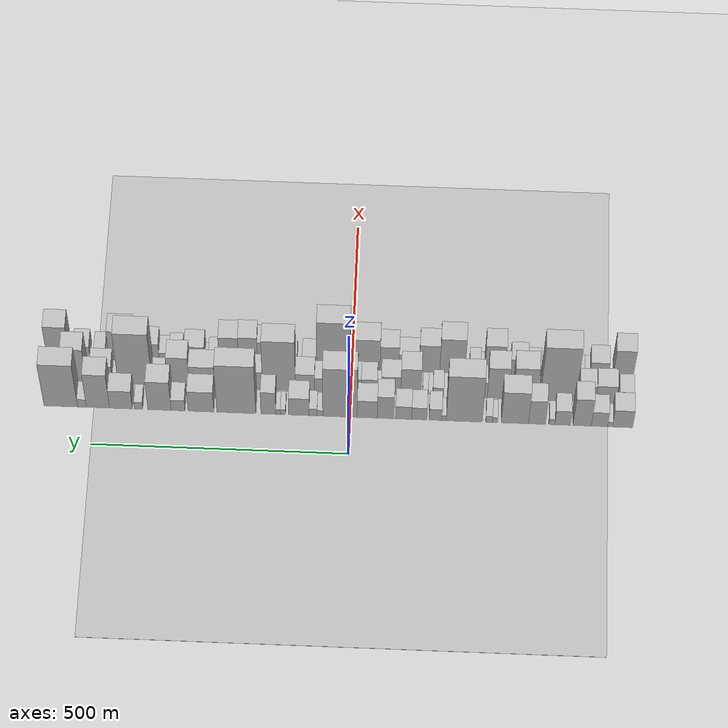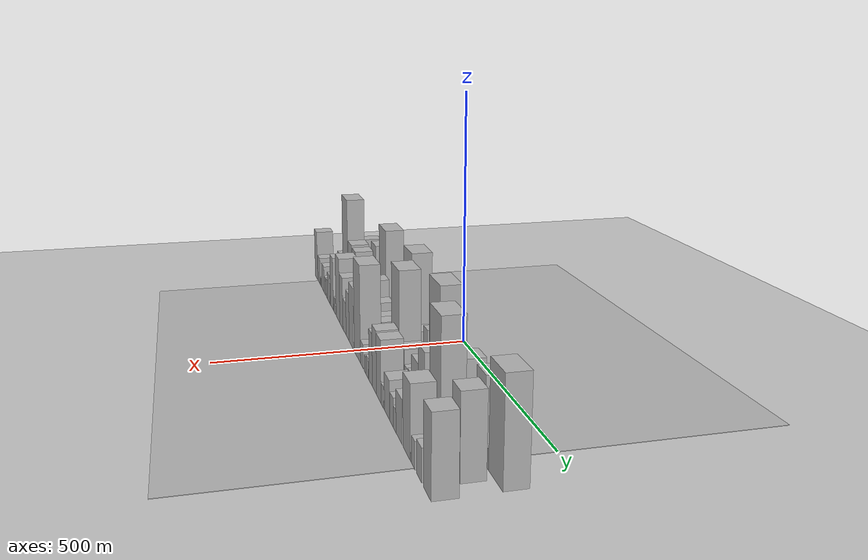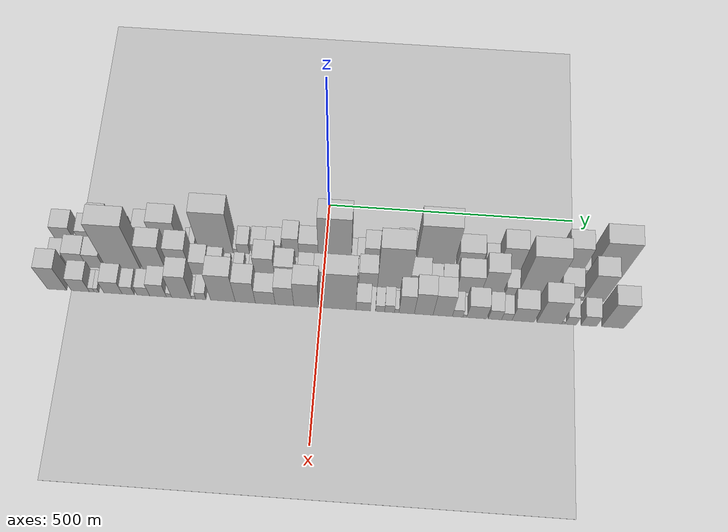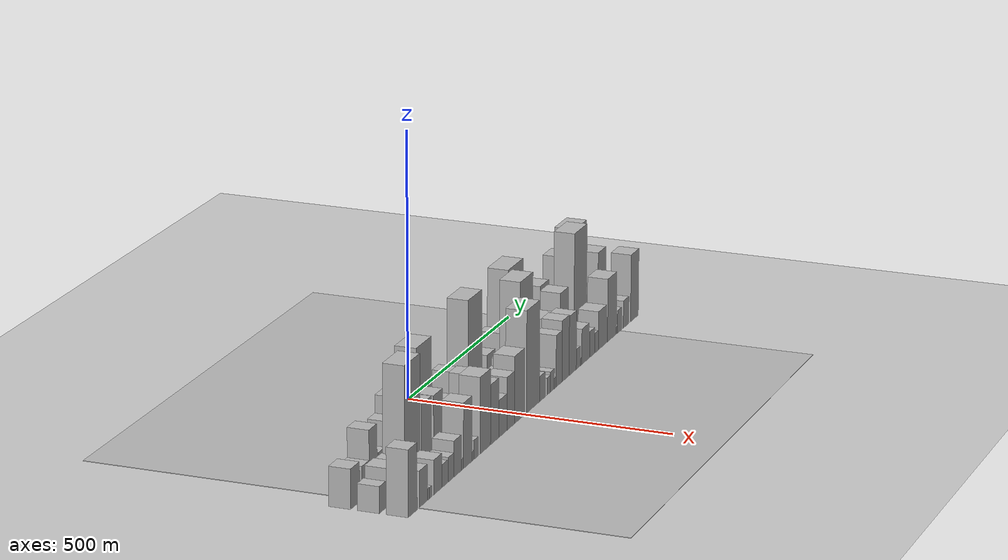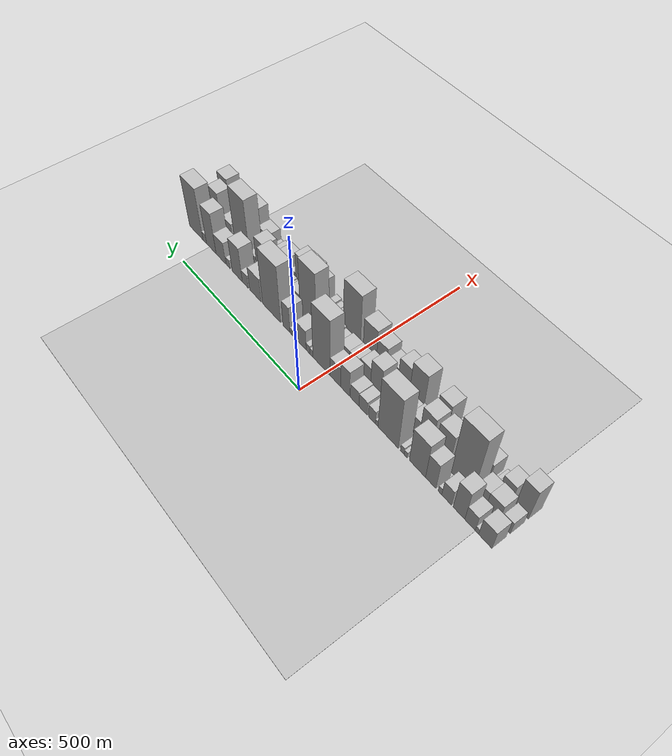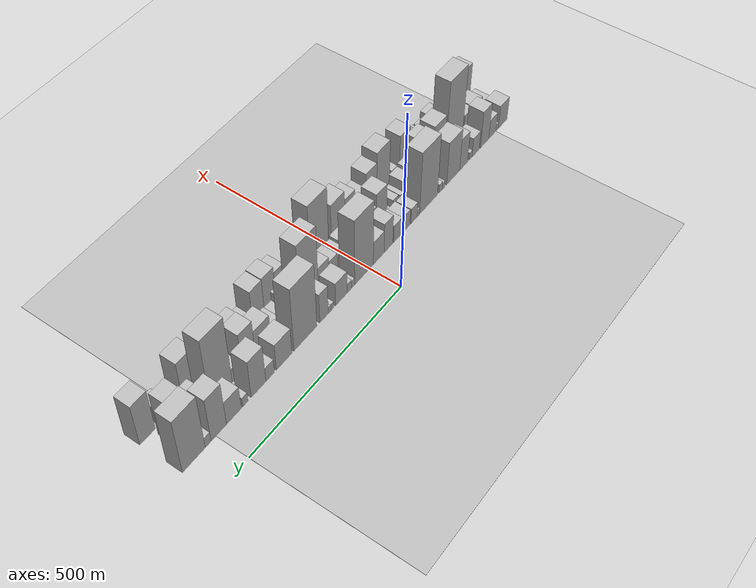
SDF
<?xml version="1.0" encoding="utf-8"?>

<sdf version="1.6">

   <world name="default">

      <gui fullscreen="0">

         <camera name="user_camera">

            <pose>-15 0 4.57585 0 0 0</pose>

            <view_controller>orbit</view_controller>

         </camera>

      </gui>

      <scene>

         <sky>

           <clouds>

             <speed>12</speed>

           </clouds>

         </sky>

         <ambient>0.4 0.4 0.4 1</ambient>

         <background>0.7 0.7 0.7 1</background>

         <shadows>1</shadows>

      </scene>

      <gravity>0 0 -9.8066</gravity>

      <magnetic_field>6e-06 2.3e-05 -4.2e-05</magnetic_field>

      <physics default="0" name="default_physics" type="ode">

         <ode>

            <solver>

               <type>quick</type>

               <iters>10</iters>

               <sor>1.0</sor>

               <use_dynamic_moi_rescaling>0</use_dynamic_moi_rescaling>

            </solver>

            <constraints>

               <cfm>0</cfm>

               <erp>0.2</erp>

               <contact_max_correcting_vel>100</contact_max_correcting_vel>

               <contact_surface_layer>0.001</contact_surface_layer>

            </constraints>

         </ode>

         <max_step_size>0.004</max_step_size>

         <real_time_factor>1</real_time_factor>

         <real_time_update_rate>250</real_time_update_rate>

      </physics>

      <light name="sun" type="directional">

         <cast_shadows>1</cast_shadows>

         <pose>0 0 10 0 0 0</pose>

         <diffuse>0.8 0.8 0.8 1</diffuse>

         <specular>0.2 0.2 0.2 1</specular>

         <attenuation>

            <range>1000</range>

            <constant>0.9</constant>

            <linear>0.01</linear>

            <quadratic>0.001</quadratic>

         </attenuation>

         <direction>-0.5 0.1 -0.9</direction>

      </light>

      <include>

         <name>ground_plane_1</name>

         <uri>model://HANNAS_ground_plane</uri>

         <pose>0 0 0  0 0 0</pose>

      </include>

      <include>

         <name>ground_plane_2</name>

         <uri>model://HANNAS_ground_plane</uri>

         <pose>100 0 0  0 0 0</pose>

      </include>

      <model name="building_1">

         <static>1</static>

         <pose frame="">100.0000 -528.5926 0 0.000000 0.000000 0.000000</pose>

         <link name="link">

            <pose frame="">0 0 36.00 0 0 0</pose>

            <collision name="collision">

               <geometry>

                  <box>

                     <size>40.0000 38.8148 72.0000</size>

                  </box>

               </geometry>

               <max_contacts>10</max_contacts>

               <surface>

                  <contact>

                     <ode/>

                  </contact>

                  <bounce/>

                  <friction>

                     <torsional>

                        <ode/>

                     </torsional>

                     <ode/>

                  </friction>

               </surface>

            </collision>

            <visual name="visual">

               <cast_shadows>0</cast_shadows>

               <geometry>

                  <box>

                     <size>40.0000 38.8148 72.0000</size>

                  </box>

               </geometry>

               <material>

                  <script>

                     <uri>model://HANNAS_wall/materials/scripts</uri>

                     <uri>model://HANNAS_wall/materials/textures</uri>

                     <name>vrc/HANNAS_wall</name>

                  </script>

               </material>

            </visual>

            <self_collide>0</self_collide>

            <enable_wind>0</enable_wind>

            <kinematic>0</kinematic>

         </link>

      </model>

      <model name="building_2">

         <static>1</static>

         <pose frame="">100.0000 -504.1947 0 0.000000 0.000000 0.000000</pose>

         <link name="link">

            <pose frame="">0 0 10.50 0 0 0</pose>

            <collision name="collision">

               <geometry>

                  <box>

                     <size>40.0000 9.9809 21.0000</size>

                  </box>

               </geometry>

               <max_contacts>10</max_contacts>

               <surface>

                  <contact>

                     <ode/>

                  </contact>

                  <bounce/>

                  <friction>

                     <torsional>

                        <ode/>

                     </torsional>

                     <ode/>

                  </friction>

               </surface>

            </collision>

            <visual name="visual">

               <cast_shadows>0</cast_shadows>

               <geometry>

                  <box>

                     <size>40.0000 9.9809 21.0000</size>

                  </box>

               </geometry>

               <material>

                  <script>

                     <uri>model://HANNAS_wall/materials/scripts</uri>

                     <uri>model://HANNAS_wall/materials/textures</uri>

                     <name>vrc/HANNAS_wall</name>

                  </script>

               </material>

            </visual>

            <self_collide>0</self_collide>

            <enable_wind>0</enable_wind>

            <kinematic>0</kinematic>

         </link>

      </model>

      <model name="building_3">

         <static>1</static>

         <pose frame="">100.0000 -483.4879 0 0.000000 0.000000 0.000000</pose>

         <link name="link">

            <pose frame="">0 0 30.00 0 0 0</pose>

            <collision name="collision">

               <geometry>

                  <box>

                     <size>40.0000 31.4326 60.0000</size>

                  </box>

               </geometry>

               <max_contacts>10</max_contacts>

               <surface>

                  <contact>

                     <ode/>

                  </contact>

                  <bounce/>

                  <friction>

                     <torsional>

                        <ode/>

                     </torsional>

                     <ode/>

                  </friction>

               </surface>

            </collision>

            <visual name="visual">

               <cast_shadows>0</cast_shadows>

               <geometry>

                  <box>

                     <size>40.0000 31.4326 60.0000</size>

                  </box>

               </geometry>

               <material>

                  <script>

                     <uri>model://HANNAS_wall/materials/scripts</uri>

                     <uri>model://HANNAS_wall/materials/textures</uri>

                     <name>vrc/HANNAS_wall</name>

                  </script>

               </material>

            </visual>

            <self_collide>0</self_collide>

            <enable_wind>0</enable_wind>

            <kinematic>0</kinematic>

         </link>

      </model>

      <model name="building_4">

         <static>1</static>

         <pose frame="">100.0000 -450.0955 0 0.000000 0.000000 0.000000</pose>

         <link name="link">

            <pose frame="">0 0 57.00 0 0 0</pose>

            <collision name="collision">

               <geometry>

                  <box>

                     <size>40.0000 35.3523 114.0000</size>

                  </box>

               </geometry>

               <max_contacts>10</max_contacts>

               <surface>

                  <contact>

                     <ode/>

                  </contact>

                  <bounce/>

                  <friction>

                     <torsional>

                        <ode/>

                     </torsional>

                     <ode/>

                  </friction>

               </surface>

            </collision>

            <visual name="visual">

               <cast_shadows>0</cast_shadows>

               <geometry>

                  <box>

                     <size>40.0000 35.3523 114.0000</size>

                  </box>

               </geometry>

               <material>

                  <script>

                     <uri>model://HANNAS_wall/materials/scripts</uri>

                     <uri>model://HANNAS_wall/materials/textures</uri>

                     <name>vrc/HANNAS_wall</name>

                  </script>

               </material>

            </visual>

            <self_collide>0</self_collide>

            <enable_wind>0</enable_wind>

            <kinematic>0</kinematic>

         </link>

      </model>

      <model name="building_5">

         <static>1</static>

         <pose frame="">100.0000 -412.2819 0 0.000000 0.000000 0.000000</pose>

         <link name="link">

            <pose frame="">0 0 30.00 0 0 0</pose>

            <collision name="collision">

               <geometry>

                  <box>

                     <size>40.0000 30.2750 60.0000</size>

                  </box>

               </geometry>

               <max_contacts>10</max_contacts>

               <surface>

                  <contact>

                     <ode/>

                  </contact>

                  <bounce/>

                  <friction>

                     <torsional>

                        <ode/>

                     </torsional>

                     <ode/>

                  </friction>

               </surface>

            </collision>

            <visual name="visual">

               <cast_shadows>0</cast_shadows>

               <geometry>

                  <box>

                     <size>40.0000 30.2750 60.0000</size>

                  </box>

               </geometry>

               <material>

                  <script>

                     <uri>model://HANNAS_wall/materials/scripts</uri>

                     <uri>model://HANNAS_wall/materials/textures</uri>

                     <name>vrc/HANNAS_wall</name>

                  </script>

               </material>

            </visual>

            <self_collide>0</self_collide>

            <enable_wind>0</enable_wind>

            <kinematic>0</kinematic>

         </link>

      </model>

      <model name="building_6">

         <static>1</static>

         <pose frame="">100.0000 -391.4086 0 0.000000 0.000000 0.000000</pose>

         <link name="link">

            <pose frame="">0 0 12.00 0 0 0</pose>

            <collision name="collision">

               <geometry>

                  <box>

                     <size>40.0000 11.4717 24.0000</size>

                  </box>

               </geometry>

               <max_contacts>10</max_contacts>

               <surface>

                  <contact>

                     <ode/>

                  </contact>

                  <bounce/>

                  <friction>

                     <torsional>

                        <ode/>

                     </torsional>

                     <ode/>

                  </friction>

               </surface>

            </collision>

            <visual name="visual">

               <cast_shadows>0</cast_shadows>

               <geometry>

                  <box>

                     <size>40.0000 11.4717 24.0000</size>

                  </box>

               </geometry>

               <material>

                  <script>

                     <uri>model://HANNAS_wall/materials/scripts</uri>

                     <uri>model://HANNAS_wall/materials/textures</uri>

                     <name>vrc/HANNAS_wall</name>

                  </script>

               </material>

            </visual>

            <self_collide>0</self_collide>

            <enable_wind>0</enable_wind>

            <kinematic>0</kinematic>

         </link>

      </model>

      <model name="building_7">

         <static>1</static>

         <pose frame="">100.0000 -362.1813 0 0.000000 0.000000 0.000000</pose>

         <link name="link">

            <pose frame="">0 0 49.50 0 0 0</pose>

            <collision name="collision">

               <geometry>

                  <box>

                     <size>40.0000 32.9830 99.0000</size>

                  </box>

               </geometry>

               <max_contacts>10</max_contacts>

               <surface>

                  <contact>

                     <ode/>

                  </contact>

                  <bounce/>

                  <friction>

                     <torsional>

                        <ode/>

                     </torsional>

                     <ode/>

                  </friction>

               </surface>

            </collision>

            <visual name="visual">

               <cast_shadows>0</cast_shadows>

               <geometry>

                  <box>

                     <size>40.0000 32.9830 99.0000</size>

                  </box>

               </geometry>

               <material>

                  <script>

                     <uri>model://HANNAS_wall/materials/scripts</uri>

                     <uri>model://HANNAS_wall/materials/textures</uri>

                     <name>vrc/HANNAS_wall</name>

                  </script>

               </material>

            </visual>

            <self_collide>0</self_collide>

            <enable_wind>0</enable_wind>

            <kinematic>0</kinematic>

         </link>

      </model>

      <model name="building_8">

         <static>1</static>

         <pose frame="">100.0000 -319.3064 0 0.000000 0.000000 0.000000</pose>

         <link name="link">

            <pose frame="">0 0 66.00 0 0 0</pose>

            <collision name="collision">

               <geometry>

                  <box>

                     <size>40.0000 52.7667 132.0000</size>

                  </box>

               </geometry>

               <max_contacts>10</max_contacts>

               <surface>

                  <contact>

                     <ode/>

                  </contact>

                  <bounce/>

                  <friction>

                     <torsional>

                        <ode/>

                     </torsional>

                     <ode/>

                  </friction>

               </surface>

            </collision>

            <visual name="visual">

               <cast_shadows>0</cast_shadows>

               <geometry>

                  <box>

                     <size>40.0000 52.7667 132.0000</size>

                  </box>

               </geometry>

               <material>

                  <script>

                     <uri>model://HANNAS_wall/materials/scripts</uri>

                     <uri>model://HANNAS_wall/materials/textures</uri>

                     <name>vrc/HANNAS_wall</name>

                  </script>

               </material>

            </visual>

            <self_collide>0</self_collide>

            <enable_wind>0</enable_wind>

            <kinematic>0</kinematic>

         </link>

      </model>

      <model name="building_9">

         <static>1</static>

         <pose frame="">100.0000 -280.9358 0 0.000000 0.000000 0.000000</pose>

         <link name="link">

            <pose frame="">0 0 10.50 0 0 0</pose>

            <collision name="collision">

               <geometry>

                  <box>

                     <size>40.0000 9.9746 21.0000</size>

                  </box>

               </geometry>

               <max_contacts>10</max_contacts>

               <surface>

                  <contact>

                     <ode/>

                  </contact>

                  <bounce/>

                  <friction>

                     <torsional>

                        <ode/>

                     </torsional>

                     <ode/>

                  </friction>

               </surface>

            </collision>

            <visual name="visual">

               <cast_shadows>0</cast_shadows>

               <geometry>

                  <box>

                     <size>40.0000 9.9746 21.0000</size>

                  </box>

               </geometry>

               <material>

                  <script>

                     <uri>model://HANNAS_wall/materials/scripts</uri>

                     <uri>model://HANNAS_wall/materials/textures</uri>

                     <name>vrc/HANNAS_wall</name>

                  </script>

               </material>

            </visual>

            <self_collide>0</self_collide>

            <enable_wind>0</enable_wind>

            <kinematic>0</kinematic>

         </link>

      </model>

      <model name="building_10">

         <static>1</static>

         <pose frame="">100.0000 -269.5451 0 0.000000 0.000000 0.000000</pose>

         <link name="link">

            <pose frame="">0 0 13.50 0 0 0</pose>

            <collision name="collision">

               <geometry>

                  <box>

                     <size>40.0000 12.8068 27.0000</size>

                  </box>

               </geometry>

               <max_contacts>10</max_contacts>

               <surface>

                  <contact>

                     <ode/>

                  </contact>

                  <bounce/>

                  <friction>

                     <torsional>

                        <ode/>

                     </torsional>

                     <ode/>

                  </friction>

               </surface>

            </collision>

            <visual name="visual">

               <cast_shadows>0</cast_shadows>

               <geometry>

                  <box>

                     <size>40.0000 12.8068 27.0000</size>

                  </box>

               </geometry>

               <material>

                  <script>

                     <uri>model://HANNAS_wall/materials/scripts</uri>

                     <uri>model://HANNAS_wall/materials/textures</uri>

                     <name>vrc/HANNAS_wall</name>

                  </script>

               </material>

            </visual>

            <self_collide>0</self_collide>

            <enable_wind>0</enable_wind>

            <kinematic>0</kinematic>

         </link>

      </model>

      <model name="building_11">

         <static>1</static>

         <pose frame="">100.0000 -221.1472 0 0.000000 0.000000 0.000000</pose>

         <link name="link">

            <pose frame="">0 0 96.00 0 0 0</pose>

            <collision name="collision">

               <geometry>

                  <box>

                     <size>40.0000 69.9890 192.0000</size>

                  </box>

               </geometry>

               <max_contacts>10</max_contacts>

               <surface>

                  <contact>

                     <ode/>

                  </contact>

                  <bounce/>

                  <friction>

                     <torsional>

                        <ode/>

                     </torsional>

                     <ode/>

                  </friction>

               </surface>

            </collision>

            <visual name="visual">

               <cast_shadows>0</cast_shadows>

               <geometry>

                  <box>

                     <size>40.0000 69.9890 192.0000</size>

                  </box>

               </geometry>

               <material>

                  <script>

                     <uri>model://HANNAS_wall/materials/scripts</uri>

                     <uri>model://HANNAS_wall/materials/textures</uri>

                     <name>vrc/HANNAS_wall</name>

                  </script>

               </material>

            </visual>

            <self_collide>0</self_collide>

            <enable_wind>0</enable_wind>

            <kinematic>0</kinematic>

         </link>

      </model>

      <model name="building_12">

         <static>1</static>

         <pose frame="">100.0000 -181.7832 0 0.000000 0.000000 0.000000</pose>

         <link name="link">

            <pose frame="">0 0 10.50 0 0 0</pose>

            <collision name="collision">

               <geometry>

                  <box>

                     <size>40.0000 8.7391 21.0000</size>

                  </box>

               </geometry>

               <max_contacts>10</max_contacts>

               <surface>

                  <contact>

                     <ode/>

                  </contact>

                  <bounce/>

                  <friction>

                     <torsional>

                        <ode/>

                     </torsional>

                     <ode/>

                  </friction>

               </surface>

            </collision>

            <visual name="visual">

               <cast_shadows>0</cast_shadows>

               <geometry>

                  <box>

                     <size>40.0000 8.7391 21.0000</size>

                  </box>

               </geometry>

               <material>

                  <script>

                     <uri>model://HANNAS_wall/materials/scripts</uri>

                     <uri>model://HANNAS_wall/materials/textures</uri>

                     <name>vrc/HANNAS_wall</name>

                  </script>

               </material>

            </visual>

            <self_collide>0</self_collide>

            <enable_wind>0</enable_wind>

            <kinematic>0</kinematic>

         </link>

      </model>

      <model name="building_13">

         <static>1</static>

         <pose frame="">100.0000 -165.0696 0 0.000000 0.000000 0.000000</pose>

         <link name="link">

            <pose frame="">0 0 24.00 0 0 0</pose>

            <collision name="collision">

               <geometry>

                  <box>

                     <size>40.0000 24.6880 48.0000</size>

                  </box>

               </geometry>

               <max_contacts>10</max_contacts>

               <surface>

                  <contact>

                     <ode/>

                  </contact>

                  <bounce/>

                  <friction>

                     <torsional>

                        <ode/>

                     </torsional>

                     <ode/>

                  </friction>

               </surface>

            </collision>

            <visual name="visual">

               <cast_shadows>0</cast_shadows>

               <geometry>

                  <box>

                     <size>40.0000 24.6880 48.0000</size>

                  </box>

               </geometry>

               <material>

                  <script>

                     <uri>model://HANNAS_wall/materials/scripts</uri>

                     <uri>model://HANNAS_wall/materials/textures</uri>

                     <name>vrc/HANNAS_wall</name>

                  </script>

               </material>

            </visual>

            <self_collide>0</self_collide>

            <enable_wind>0</enable_wind>

            <kinematic>0</kinematic>

         </link>

      </model>

      <model name="building_14">

         <static>1</static>

         <pose frame="">100.0000 -133.9013 0 0.000000 0.000000 0.000000</pose>

         <link name="link">

            <pose frame="">0 0 25.50 0 0 0</pose>

            <collision name="collision">

               <geometry>

                  <box>

                     <size>40.0000 29.6487 51.0000</size>

                  </box>

               </geometry>

               <max_contacts>10</max_contacts>

               <surface>

                  <contact>

                     <ode/>

                  </contact>

                  <bounce/>

                  <friction>

                     <torsional>

                        <ode/>

                     </torsional>

                     <ode/>

                  </friction>

               </surface>

            </collision>

            <visual name="visual">

               <cast_shadows>0</cast_shadows>

               <geometry>

                  <box>

                     <size>40.0000 29.6487 51.0000</size>

                  </box>

               </geometry>

               <material>

                  <script>

                     <uri>model://HANNAS_wall/materials/scripts</uri>

                     <uri>model://HANNAS_wall/materials/textures</uri>

                     <name>vrc/HANNAS_wall</name>

                  </script>

               </material>

            </visual>

            <self_collide>0</self_collide>

            <enable_wind>0</enable_wind>

            <kinematic>0</kinematic>

         </link>

      </model>

      <model name="building_15">

         <static>1</static>

         <pose frame="">100.0000 -103.3088 0 0.000000 0.000000 0.000000</pose>

         <link name="link">

            <pose frame="">0 0 27.00 0 0 0</pose>

            <collision name="collision">

               <geometry>

                  <box>

                     <size>40.0000 31.5362 54.0000</size>

                  </box>

               </geometry>

               <max_contacts>10</max_contacts>

               <surface>

                  <contact>

                     <ode/>

                  </contact>

                  <bounce/>

                  <friction>

                     <torsional>

                        <ode/>

                     </torsional>

                     <ode/>

                  </friction>

               </surface>

            </collision>

            <visual name="visual">

               <cast_shadows>0</cast_shadows>

               <geometry>

                  <box>

                     <size>40.0000 31.5362 54.0000</size>

                  </box>

               </geometry>

               <material>

                  <script>

                     <uri>model://HANNAS_wall/materials/scripts</uri>

                     <uri>model://HANNAS_wall/materials/textures</uri>

                     <name>vrc/HANNAS_wall</name>

                  </script>

               </material>

            </visual>

            <self_collide>0</self_collide>

            <enable_wind>0</enable_wind>

            <kinematic>0</kinematic>

         </link>

      </model>

      <model name="building_16">

         <static>1</static>

         <pose frame="">100.0000 -68.3457 0 0.000000 0.000000 0.000000</pose>

         <link name="link">

            <pose frame="">0 0 46.50 0 0 0</pose>

            <collision name="collision">

               <geometry>

                  <box>

                     <size>40.0000 32.3901 93.0000</size>

                  </box>

               </geometry>

               <max_contacts>10</max_contacts>

               <surface>

                  <contact>

                     <ode/>

                  </contact>

                  <bounce/>

                  <friction>

                     <torsional>

                        <ode/>

                     </torsional>

                     <ode/>

                  </friction>

               </surface>

            </collision>

            <visual name="visual">

               <cast_shadows>0</cast_shadows>

               <geometry>

                  <box>

                     <size>40.0000 32.3901 93.0000</size>

                  </box>

               </geometry>

               <material>

                  <script>

                     <uri>model://HANNAS_wall/materials/scripts</uri>

                     <uri>model://HANNAS_wall/materials/textures</uri>

                     <name>vrc/HANNAS_wall</name>

                  </script>

               </material>

            </visual>

            <self_collide>0</self_collide>

            <enable_wind>0</enable_wind>

            <kinematic>0</kinematic>

         </link>

      </model>

      <model name="building_17">

         <static>1</static>

         <pose frame="">100.0000 -32.6215 0 0.000000 0.000000 0.000000</pose>

         <link name="link">

            <pose frame="">0 0 36.00 0 0 0</pose>

            <collision name="collision">

               <geometry>

                  <box>

                     <size>40.0000 39.0583 72.0000</size>

                  </box>

               </geometry>

               <max_contacts>10</max_contacts>

               <surface>

                  <contact>

                     <ode/>

                  </contact>

                  <bounce/>

                  <friction>

                     <torsional>

                        <ode/>

                     </torsional>

                     <ode/>

                  </friction>

               </surface>

            </collision>

            <visual name="visual">

               <cast_shadows>0</cast_shadows>

               <geometry>

                  <box>

                     <size>40.0000 39.0583 72.0000</size>

                  </box>

               </geometry>

               <material>

                  <script>

                     <uri>model://HANNAS_wall/materials/scripts</uri>

                     <uri>model://HANNAS_wall/materials/textures</uri>

                     <name>vrc/HANNAS_wall</name>

                  </script>

               </material>

            </visual>

            <self_collide>0</self_collide>

            <enable_wind>0</enable_wind>

            <kinematic>0</kinematic>

         </link>

      </model>

      <model name="building_18">

         <static>1</static>

         <pose frame="">100.0000 20.3426 0 0.000000 0.000000 0.000000</pose>

         <link name="link">

            <pose frame="">0 0 102.00 0 0 0</pose>

            <collision name="collision">

               <geometry>

                  <box>

                     <size>40.0000 66.8698 204.0000</size>

                  </box>

               </geometry>

               <max_contacts>10</max_contacts>

               <surface>

                  <contact>

                     <ode/>

                  </contact>

                  <bounce/>

                  <friction>

                     <torsional>

                        <ode/>

                     </torsional>

                     <ode/>

                  </friction>

               </surface>

            </collision>

            <visual name="visual">

               <cast_shadows>0</cast_shadows>

               <geometry>

                  <box>

                     <size>40.0000 66.8698 204.0000</size>

                  </box>

               </geometry>

               <material>

                  <script>

                     <uri>model://HANNAS_wall/materials/scripts</uri>

                     <uri>model://HANNAS_wall/materials/textures</uri>

                     <name>vrc/HANNAS_wall</name>

                  </script>

               </material>

            </visual>

            <self_collide>0</self_collide>

            <enable_wind>0</enable_wind>

            <kinematic>0</kinematic>

         </link>

      </model>

      <model name="building_19">

         <static>1</static>

         <pose frame="">100.0000 59.2627 0 0.000000 0.000000 0.000000</pose>

         <link name="link">

            <pose frame="">0 0 12.00 0 0 0</pose>

            <collision name="collision">

               <geometry>

                  <box>

                     <size>40.0000 10.9704 24.0000</size>

                  </box>

               </geometry>

               <max_contacts>10</max_contacts>

               <surface>

                  <contact>

                     <ode/>

                  </contact>

                  <bounce/>

                  <friction>

                     <torsional>

                        <ode/>

                     </torsional>

                     <ode/>

                  </friction>

               </surface>

            </collision>

            <visual name="visual">

               <cast_shadows>0</cast_shadows>

               <geometry>

                  <box>

                     <size>40.0000 10.9704 24.0000</size>

                  </box>

               </geometry>

               <material>

                  <script>

                     <uri>model://HANNAS_wall/materials/scripts</uri>

                     <uri>model://HANNAS_wall/materials/textures</uri>

                     <name>vrc/HANNAS_wall</name>

                  </script>

               </material>

            </visual>

            <self_collide>0</self_collide>

            <enable_wind>0</enable_wind>

            <kinematic>0</kinematic>

         </link>

      </model>

      <model name="building_20">

         <static>1</static>

         <pose frame="">100.0000 72.4985 0 0.000000 0.000000 0.000000</pose>

         <link name="link">

            <pose frame="">0 0 15.00 0 0 0</pose>

            <collision name="collision">

               <geometry>

                  <box>

                     <size>40.0000 15.5013 30.0000</size>

                  </box>

               </geometry>

               <max_contacts>10</max_contacts>

               <surface>

                  <contact>

                     <ode/>

                  </contact>

                  <bounce/>

                  <friction>

                     <torsional>

                        <ode/>

                     </torsional>

                     <ode/>

                  </friction>

               </surface>

            </collision>

            <visual name="visual">

               <cast_shadows>0</cast_shadows>

               <geometry>

                  <box>

                     <size>40.0000 15.5013 30.0000</size>

                  </box>

               </geometry>

               <material>

                  <script>

                     <uri>model://HANNAS_wall/materials/scripts</uri>

                     <uri>model://HANNAS_wall/materials/textures</uri>

                     <name>vrc/HANNAS_wall</name>

                  </script>

               </material>

            </visual>

            <self_collide>0</self_collide>

            <enable_wind>0</enable_wind>

            <kinematic>0</kinematic>

         </link>

      </model>

      <model name="building_21">

         <static>1</static>

         <pose frame="">100.0000 100.2305 0 0.000000 0.000000 0.000000</pose>

         <link name="link">

            <pose frame="">0 0 36.00 0 0 0</pose>

            <collision name="collision">

               <geometry>

                  <box>

                     <size>40.0000 39.9627 72.0000</size>

                  </box>

               </geometry>

               <max_contacts>10</max_contacts>

               <surface>

                  <contact>

                     <ode/>

                  </contact>

                  <bounce/>

                  <friction>

                     <torsional>

                        <ode/>

                     </torsional>

                     <ode/>

                  </friction>

               </surface>

            </collision>

            <visual name="visual">

               <cast_shadows>0</cast_shadows>

               <geometry>

                  <box>

                     <size>40.0000 39.9627 72.0000</size>

                  </box>

               </geometry>

               <material>

                  <script>

                     <uri>model://HANNAS_wall/materials/scripts</uri>

                     <uri>model://HANNAS_wall/materials/textures</uri>

                     <name>vrc/HANNAS_wall</name>

                  </script>

               </material>

            </visual>

            <self_collide>0</self_collide>

            <enable_wind>0</enable_wind>

            <kinematic>0</kinematic>

         </link>

      </model>

      <model name="building_22">

         <static>1</static>

         <pose frame="">100.0000 131.3151 0 0.000000 0.000000 0.000000</pose>

         <link name="link">

            <pose frame="">0 0 10.50 0 0 0</pose>

            <collision name="collision">

               <geometry>

                  <box>

                     <size>40.0000 10.2065 21.0000</size>

                  </box>

               </geometry>

               <max_contacts>10</max_contacts>

               <surface>

                  <contact>

                     <ode/>

                  </contact>

                  <bounce/>

                  <friction>

                     <torsional>

                        <ode/>

                     </torsional>

                     <ode/>

                  </friction>

               </surface>

            </collision>

            <visual name="visual">

               <cast_shadows>0</cast_shadows>

               <geometry>

                  <box>

                     <size>40.0000 10.2065 21.0000</size>

                  </box>

               </geometry>

               <material>

                  <script>

                     <uri>model://HANNAS_wall/materials/scripts</uri>

                     <uri>model://HANNAS_wall/materials/textures</uri>

                     <name>vrc/HANNAS_wall</name>

                  </script>

               </material>

            </visual>

            <self_collide>0</self_collide>

            <enable_wind>0</enable_wind>

            <kinematic>0</kinematic>

         </link>

      </model>

      <model name="building_23">

         <static>1</static>

         <pose frame="">100.0000 140.7610 0 0.000000 0.000000 0.000000</pose>

         <link name="link">

            <pose frame="">0 0 10.50 0 0 0</pose>

            <collision name="collision">

               <geometry>

                  <box>

                     <size>40.0000 8.6855 21.0000</size>

                  </box>

               </geometry>

               <max_contacts>10</max_contacts>

               <surface>

                  <contact>

                     <ode/>

                  </contact>

                  <bounce/>

                  <friction>

                     <torsional>

                        <ode/>

                     </torsional>

                     <ode/>

                  </friction>

               </surface>

            </collision>

            <visual name="visual">

               <cast_shadows>0</cast_shadows>

               <geometry>

                  <box>

                     <size>40.0000 8.6855 21.0000</size>

                  </box>

               </geometry>

               <material>

                  <script>

                     <uri>model://HANNAS_wall/materials/scripts</uri>

                     <uri>model://HANNAS_wall/materials/textures</uri>

                     <name>vrc/HANNAS_wall</name>

                  </script>

               </material>

            </visual>

            <self_collide>0</self_collide>

            <enable_wind>0</enable_wind>

            <kinematic>0</kinematic>

         </link>

      </model>

      <model name="building_24">

         <static>1</static>

         <pose frame="">100.0000 159.5130 0 0.000000 0.000000 0.000000</pose>

         <link name="link">

            <pose frame="">0 0 46.50 0 0 0</pose>

            <collision name="collision">

               <geometry>

                  <box>

                     <size>40.0000 28.8184 93.0000</size>

                  </box>

               </geometry>

               <max_contacts>10</max_contacts>

               <surface>

                  <contact>

                     <ode/>

                  </contact>

                  <bounce/>

                  <friction>

                     <torsional>

                        <ode/>

                     </torsional>

                     <ode/>

                  </friction>

               </surface>

            </collision>

            <visual name="visual">

               <cast_shadows>0</cast_shadows>

               <geometry>

                  <box>

                     <size>40.0000 28.8184 93.0000</size>

                  </box>

               </geometry>

               <material>

                  <script>

                     <uri>model://HANNAS_wall/materials/scripts</uri>

                     <uri>model://HANNAS_wall/materials/textures</uri>

                     <name>vrc/HANNAS_wall</name>

                  </script>

               </material>

            </visual>

            <self_collide>0</self_collide>

            <enable_wind>0</enable_wind>

            <kinematic>0</kinematic>

         </link>

      </model>

      <model name="building_25">

         <static>1</static>

         <pose frame="">100.0000 221.8698 0 0.000000 0.000000 0.000000</pose>

         <link name="link">

            <pose frame="">0 0 100.50 0 0 0</pose>

            <collision name="collision">

               <geometry>

                  <box>

                     <size>40.0000 75.8951 201.0000</size>

                  </box>

               </geometry>

               <max_contacts>10</max_contacts>

               <surface>

                  <contact>

                     <ode/>

                  </contact>

                  <bounce/>

                  <friction>

                     <torsional>

                        <ode/>

                     </torsional>

                     <ode/>

                  </friction>

               </surface>

            </collision>

            <visual name="visual">

               <cast_shadows>0</cast_shadows>

               <geometry>

                  <box>

                     <size>40.0000 75.8951 201.0000</size>

                  </box>

               </geometry>

               <material>

                  <script>

                     <uri>model://HANNAS_wall/materials/scripts</uri>

                     <uri>model://HANNAS_wall/materials/textures</uri>

                     <name>vrc/HANNAS_wall</name>

                  </script>

               </material>

            </visual>

            <self_collide>0</self_collide>

            <enable_wind>0</enable_wind>

            <kinematic>0</kinematic>

         </link>

      </model>

      <model name="building_26">

         <static>1</static>

         <pose frame="">100.0000 290.8363 0 0.000000 0.000000 0.000000</pose>

         <link name="link">

            <pose frame="">0 0 42.00 0 0 0</pose>

            <collision name="collision">

               <geometry>

                  <box>

                     <size>40.0000 50.0380 84.0000</size>

                  </box>

               </geometry>

               <max_contacts>10</max_contacts>

               <surface>

                  <contact>

                     <ode/>

                  </contact>

                  <bounce/>

                  <friction>

                     <torsional>

                        <ode/>

                     </torsional>

                     <ode/>

                  </friction>

               </surface>

            </collision>

            <visual name="visual">

               <cast_shadows>0</cast_shadows>

               <geometry>

                  <box>

                     <size>40.0000 50.0380 84.0000</size>

                  </box>

               </geometry>

               <material>

                  <script>

                     <uri>model://HANNAS_wall/materials/scripts</uri>

                     <uri>model://HANNAS_wall/materials/textures</uri>

                     <name>vrc/HANNAS_wall</name>

                  </script>

               </material>

            </visual>

            <self_collide>0</self_collide>

            <enable_wind>0</enable_wind>

            <kinematic>0</kinematic>

         </link>

      </model>

      <model name="building_27">

         <static>1</static>

         <pose frame="">100.0000 335.2928 0 0.000000 0.000000 0.000000</pose>

         <link name="link">

            <pose frame="">0 0 22.50 0 0 0</pose>

            <collision name="collision">

               <geometry>

                  <box>

                     <size>40.0000 26.8749 45.0000</size>

                  </box>

               </geometry>

               <max_contacts>10</max_contacts>

               <surface>

                  <contact>

                     <ode/>

                  </contact>

                  <bounce/>

                  <friction>

                     <torsional>

                        <ode/>

                     </torsional>

                     <ode/>

                  </friction>

               </surface>

            </collision>

            <visual name="visual">

               <cast_shadows>0</cast_shadows>

               <geometry>

                  <box>

                     <size>40.0000 26.8749 45.0000</size>

                  </box>

               </geometry>

               <material>

                  <script>

                     <uri>model://HANNAS_wall/materials/scripts</uri>

                     <uri>model://HANNAS_wall/materials/textures</uri>

                     <name>vrc/HANNAS_wall</name>

                  </script>

               </material>

            </visual>

            <self_collide>0</self_collide>

            <enable_wind>0</enable_wind>

            <kinematic>0</kinematic>

         </link>

      </model>

      <model name="building_28">

         <static>1</static>

         <pose frame="">100.0000 371.4529 0 0.000000 0.000000 0.000000</pose>

         <link name="link">

            <pose frame="">0 0 60.00 0 0 0</pose>

            <collision name="collision">

               <geometry>

                  <box>

                     <size>40.0000 45.4452 120.0000</size>

                  </box>

               </geometry>

               <max_contacts>10</max_contacts>

               <surface>

                  <contact>

                     <ode/>

                  </contact>

                  <bounce/>

                  <friction>

                     <torsional>

                        <ode/>

                     </torsional>

                     <ode/>

                  </friction>

               </surface>

            </collision>

            <visual name="visual">

               <cast_shadows>0</cast_shadows>

               <geometry>

                  <box>

                     <size>40.0000 45.4452 120.0000</size>

                  </box>

               </geometry>

               <material>

                  <script>

                     <uri>model://HANNAS_wall/materials/scripts</uri>

                     <uri>model://HANNAS_wall/materials/textures</uri>

                     <name>vrc/HANNAS_wall</name>

                  </script>

               </material>

            </visual>

            <self_collide>0</self_collide>

            <enable_wind>0</enable_wind>

            <kinematic>0</kinematic>

         </link>

      </model>

      <model name="building_29">

         <static>1</static>

         <pose frame="">100.0000 412.3087 0 0.000000 0.000000 0.000000</pose>

         <link name="link">

            <pose frame="">0 0 15.00 0 0 0</pose>

            <collision name="collision">

               <geometry>

                  <box>

                     <size>40.0000 16.2664 30.0000</size>

                  </box>

               </geometry>

               <max_contacts>10</max_contacts>

               <surface>

                  <contact>

                     <ode/>

                  </contact>

                  <bounce/>

                  <friction>

                     <torsional>

                        <ode/>

                     </torsional>

                     <ode/>

                  </friction>

               </surface>

            </collision>

            <visual name="visual">

               <cast_shadows>0</cast_shadows>

               <geometry>

                  <box>

                     <size>40.0000 16.2664 30.0000</size>

                  </box>

               </geometry>

               <material>

                  <script>

                     <uri>model://HANNAS_wall/materials/scripts</uri>

                     <uri>model://HANNAS_wall/materials/textures</uri>

                     <name>vrc/HANNAS_wall</name>

                  </script>

               </material>

            </visual>

            <self_collide>0</self_collide>

            <enable_wind>0</enable_wind>

            <kinematic>0</kinematic>

         </link>

      </model>

      <model name="building_30">

         <static>1</static>

         <pose frame="">100.0000 446.6647 0 0.000000 0.000000 0.000000</pose>

         <link name="link">

            <pose frame="">0 0 37.50 0 0 0</pose>

            <collision name="collision">

               <geometry>

                  <box>

                     <size>40.0000 44.4457 75.0000</size>

                  </box>

               </geometry>

               <max_contacts>10</max_contacts>

               <surface>

                  <contact>

                     <ode/>

                  </contact>

                  <bounce/>

                  <friction>

                     <torsional>

                        <ode/>

                     </torsional>

                     <ode/>

                  </friction>

               </surface>

            </collision>

            <visual name="visual">

               <cast_shadows>0</cast_shadows>

               <geometry>

                  <box>

                     <size>40.0000 44.4457 75.0000</size>

                  </box>

               </geometry>

               <material>

                  <script>

                     <uri>model://HANNAS_wall/materials/scripts</uri>

                     <uri>model://HANNAS_wall/materials/textures</uri>

                     <name>vrc/HANNAS_wall</name>

                  </script>

               </material>

            </visual>

            <self_collide>0</self_collide>

            <enable_wind>0</enable_wind>

            <kinematic>0</kinematic>

         </link>

      </model>

      <model name="building_31">

         <static>1</static>

         <pose frame="">100.0000 491.4737 0 0.000000 0.000000 0.000000</pose>

         <link name="link">

            <pose frame="">0 0 70.50 0 0 0</pose>

            <collision name="collision">

               <geometry>

                  <box>

                     <size>40.0000 45.1723 141.0000</size>

                  </box>

               </geometry>

               <max_contacts>10</max_contacts>

               <surface>

                  <contact>

                     <ode/>

                  </contact>

                  <bounce/>

                  <friction>

                     <torsional>

                        <ode/>

                     </torsional>

                     <ode/>

                  </friction>

               </surface>

            </collision>

            <visual name="visual">

               <cast_shadows>0</cast_shadows>

               <geometry>

                  <box>

                     <size>40.0000 45.1723 141.0000</size>

                  </box>

               </geometry>

               <material>

                  <script>

                     <uri>model://HANNAS_wall/materials/scripts</uri>

                     <uri>model://HANNAS_wall/materials/textures</uri>

                     <name>vrc/HANNAS_wall</name>

                  </script>

               </material>

            </visual>

            <self_collide>0</self_collide>

            <enable_wind>0</enable_wind>

            <kinematic>0</kinematic>

         </link>

      </model>

      <model name="building_32">

         <static>1</static>

         <pose frame="">100.0000 522.6050 0 0.000000 0.000000 0.000000</pose>

         <link name="link">

            <pose frame="">0 0 16.50 0 0 0</pose>

            <collision name="collision">

               <geometry>

                  <box>

                     <size>40.0000 17.0903 33.0000</size>

                  </box>

               </geometry>

               <max_contacts>10</max_contacts>

               <surface>

                  <contact>

                     <ode/>

                  </contact>

                  <bounce/>

                  <friction>

                     <torsional>

                        <ode/>

                     </torsional>

                     <ode/>

                  </friction>

               </surface>

            </collision>

            <visual name="visual">

               <cast_shadows>0</cast_shadows>

               <geometry>

                  <box>

                     <size>40.0000 17.0903 33.0000</size>

                  </box>

               </geometry>

               <material>

                  <script>

                     <uri>model://HANNAS_wall/materials/scripts</uri>

                     <uri>model://HANNAS_wall/materials/textures</uri>

                     <name>vrc/HANNAS_wall</name>

                  </script>

               </material>

            </visual>

            <self_collide>0</self_collide>

            <enable_wind>0</enable_wind>

            <kinematic>0</kinematic>

         </link>

      </model>

      <model name="building_33">

         <static>1</static>

         <pose frame="">100.0000 563.8923 0 0.000000 0.000000 0.000000</pose>

         <link name="link">

            <pose frame="">0 0 88.50 0 0 0</pose>

            <collision name="collision">

               <geometry>

                  <box>

                     <size>40.0000 65.4842 177.0000</size>

                  </box>

               </geometry>

               <max_contacts>10</max_contacts>

               <surface>

                  <contact>

                     <ode/>

                  </contact>

                  <bounce/>

                  <friction>

                     <torsional>

                        <ode/>

                     </torsional>

                     <ode/>

                  </friction>

               </surface>

            </collision>

            <visual name="visual">

               <cast_shadows>0</cast_shadows>

               <geometry>

                  <box>

                     <size>40.0000 65.4842 177.0000</size>

                  </box>

               </geometry>

               <material>

                  <script>

                     <uri>model://HANNAS_wall/materials/scripts</uri>

                     <uri>model://HANNAS_wall/materials/textures</uri>

                     <name>vrc/HANNAS_wall</name>

                  </script>

               </material>

            </visual>

            <self_collide>0</self_collide>

            <enable_wind>0</enable_wind>

            <kinematic>0</kinematic>

         </link>

      </model>

      <model name="building_34">

         <static>1</static>

         <pose frame="">152.0000 -533.8637 0 0.000000 0.000000 0.000000</pose>

         <link name="link">

            <pose frame="">0 0 24.00 0 0 0</pose>

            <collision name="collision">

               <geometry>

                  <box>

                     <size>40.0000 28.2725 48.0000</size>

                  </box>

               </geometry>

               <max_contacts>10</max_contacts>

               <surface>

                  <contact>

                     <ode/>

                  </contact>

                  <bounce/>

                  <friction>

                     <torsional>

                        <ode/>

                     </torsional>

                     <ode/>

                  </friction>

               </surface>

            </collision>

            <visual name="visual">

               <cast_shadows>0</cast_shadows>

               <geometry>

                  <box>

                     <size>40.0000 28.2725 48.0000</size>

                  </box>

               </geometry>

               <material>

                  <script>

                     <uri>model://HANNAS_wall/materials/scripts</uri>

                     <uri>model://HANNAS_wall/materials/textures</uri>

                     <name>vrc/HANNAS_wall</name>

                  </script>

               </material>

            </visual>

            <self_collide>0</self_collide>

            <enable_wind>0</enable_wind>

            <kinematic>0</kinematic>

         </link>

      </model>

      <model name="building_35">

         <static>1</static>

         <pose frame="">152.0000 -495.7774 0 0.000000 0.000000 0.000000</pose>

         <link name="link">

            <pose frame="">0 0 34.50 0 0 0</pose>

            <collision name="collision">

               <geometry>

                  <box>

                     <size>40.0000 39.9002 69.0000</size>

                  </box>

               </geometry>

               <max_contacts>10</max_contacts>

               <surface>

                  <contact>

                     <ode/>

                  </contact>

                  <bounce/>

                  <friction>

                     <torsional>

                        <ode/>

                     </torsional>

                     <ode/>

                  </friction>

               </surface>

            </collision>

            <visual name="visual">

               <cast_shadows>0</cast_shadows>

               <geometry>

                  <box>

                     <size>40.0000 39.9002 69.0000</size>

                  </box>

               </geometry>

               <material>

                  <script>

                     <uri>model://HANNAS_wall/materials/scripts</uri>

                     <uri>model://HANNAS_wall/materials/textures</uri>

                     <name>vrc/HANNAS_wall</name>

                  </script>

               </material>

            </visual>

            <self_collide>0</self_collide>

            <enable_wind>0</enable_wind>

            <kinematic>0</kinematic>

         </link>

      </model>

      <model name="building_36">

         <static>1</static>

         <pose frame="">152.0000 -458.9496 0 0.000000 0.000000 0.000000</pose>

         <link name="link">

            <pose frame="">0 0 33.00 0 0 0</pose>

            <collision name="collision">

               <geometry>

                  <box>

                     <size>40.0000 33.7553 66.0000</size>

                  </box>

               </geometry>

               <max_contacts>10</max_contacts>

               <surface>

                  <contact>

                     <ode/>

                  </contact>

                  <bounce/>

                  <friction>

                     <torsional>

                        <ode/>

                     </torsional>

                     <ode/>

                  </friction>

               </surface>

            </collision>

            <visual name="visual">

               <cast_shadows>0</cast_shadows>

               <geometry>

                  <box>

                     <size>40.0000 33.7553 66.0000</size>

                  </box>

               </geometry>

               <material>

                  <script>

                     <uri>model://HANNAS_wall/materials/scripts</uri>

                     <uri>model://HANNAS_wall/materials/textures</uri>

                     <name>vrc/HANNAS_wall</name>

                  </script>

               </material>

            </visual>

            <self_collide>0</self_collide>

            <enable_wind>0</enable_wind>

            <kinematic>0</kinematic>

         </link>

      </model>

      <model name="building_37">

         <static>1</static>

         <pose frame="">152.0000 -402.2357 0 0.000000 0.000000 0.000000</pose>

         <link name="link">

            <pose frame="">0 0 112.50 0 0 0</pose>

            <collision name="collision">

               <geometry>

                  <box>

                     <size>40.0000 69.6724 225.0000</size>

                  </box>

               </geometry>

               <max_contacts>10</max_contacts>

               <surface>

                  <contact>

                     <ode/>

                  </contact>

                  <bounce/>

                  <friction>

                     <torsional>

                        <ode/>

                     </torsional>

                     <ode/>

                  </friction>

               </surface>

            </collision>

            <visual name="visual">

               <cast_shadows>0</cast_shadows>

               <geometry>

                  <box>

                     <size>40.0000 69.6724 225.0000</size>

                  </box>

               </geometry>

               <material>

                  <script>

                     <uri>model://HANNAS_wall/materials/scripts</uri>

                     <uri>model://HANNAS_wall/materials/textures</uri>

                     <name>vrc/HANNAS_wall</name>

                  </script>

               </material>

            </visual>

            <self_collide>0</self_collide>

            <enable_wind>0</enable_wind>

            <kinematic>0</kinematic>

         </link>

      </model>

      <model name="building_38">

         <static>1</static>

         <pose frame="">152.0000 -338.3357 0 0.000000 0.000000 0.000000</pose>

         <link name="link">

            <pose frame="">0 0 66.00 0 0 0</pose>

            <collision name="collision">

               <geometry>

                  <box>

                     <size>40.0000 46.1275 132.0000</size>

                  </box>

               </geometry>

               <max_contacts>10</max_contacts>

               <surface>

                  <contact>

                     <ode/>

                  </contact>

                  <bounce/>

                  <friction>

                     <torsional>

                        <ode/>

                     </torsional>

                     <ode/>

                  </friction>

               </surface>

            </collision>

            <visual name="visual">

               <cast_shadows>0</cast_shadows>

               <geometry>

                  <box>

                     <size>40.0000 46.1275 132.0000</size>

                  </box>

               </geometry>

               <material>

                  <script>

                     <uri>model://HANNAS_wall/materials/scripts</uri>

                     <uri>model://HANNAS_wall/materials/textures</uri>

                     <name>vrc/HANNAS_wall</name>

                  </script>

               </material>

            </visual>

            <self_collide>0</self_collide>

            <enable_wind>0</enable_wind>

            <kinematic>0</kinematic>

         </link>

      </model>

      <model name="building_39">

         <static>1</static>

         <pose frame="">152.0000 -285.3753 0 0.000000 0.000000 0.000000</pose>

         <link name="link">

            <pose frame="">0 0 64.50 0 0 0</pose>

            <collision name="collision">

               <geometry>

                  <box>

                     <size>40.0000 41.7935 129.0000</size>

                  </box>

               </geometry>

               <max_contacts>10</max_contacts>

               <surface>

                  <contact>

                     <ode/>

                  </contact>

                  <bounce/>

                  <friction>

                     <torsional>

                        <ode/>

                     </torsional>

                     <ode/>

                  </friction>

               </surface>

            </collision>

            <visual name="visual">

               <cast_shadows>0</cast_shadows>

               <geometry>

                  <box>

                     <size>40.0000 41.7935 129.0000</size>

                  </box>

               </geometry>

               <material>

                  <script>

                     <uri>model://HANNAS_wall/materials/scripts</uri>

                     <uri>model://HANNAS_wall/materials/textures</uri>

                     <name>vrc/HANNAS_wall</name>

                  </script>

               </material>

            </visual>

            <self_collide>0</self_collide>

            <enable_wind>0</enable_wind>

            <kinematic>0</kinematic>

         </link>

      </model>

      <model name="building_40">

         <static>1</static>

         <pose frame="">152.0000 -247.9603 0 0.000000 0.000000 0.000000</pose>

         <link name="link">

            <pose frame="">0 0 33.00 0 0 0</pose>

            <collision name="collision">

               <geometry>

                  <box>

                     <size>40.0000 33.0364 66.0000</size>

                  </box>

               </geometry>

               <max_contacts>10</max_contacts>

               <surface>

                  <contact>

                     <ode/>

                  </contact>

                  <bounce/>

                  <friction>

                     <torsional>

                        <ode/>

                     </torsional>

                     <ode/>

                  </friction>

               </surface>

            </collision>

            <visual name="visual">

               <cast_shadows>0</cast_shadows>

               <geometry>

                  <box>

                     <size>40.0000 33.0364 66.0000</size>

                  </box>

               </geometry>

               <material>

                  <script>

                     <uri>model://HANNAS_wall/materials/scripts</uri>

                     <uri>model://HANNAS_wall/materials/textures</uri>

                     <name>vrc/HANNAS_wall</name>

                  </script>

               </material>

            </visual>

            <self_collide>0</self_collide>

            <enable_wind>0</enable_wind>

            <kinematic>0</kinematic>

         </link>

      </model>

      <model name="building_41">

         <static>1</static>

         <pose frame="">152.0000 -215.9658 0 0.000000 0.000000 0.000000</pose>

         <link name="link">

            <pose frame="">0 0 28.50 0 0 0</pose>

            <collision name="collision">

               <geometry>

                  <box>

                     <size>40.0000 30.9527 57.0000</size>

                  </box>

               </geometry>

               <max_contacts>10</max_contacts>

               <surface>

                  <contact>

                     <ode/>

                  </contact>

                  <bounce/>

                  <friction>

                     <torsional>

                        <ode/>

                     </torsional>

                     <ode/>

                  </friction>

               </surface>

            </collision>

            <visual name="visual">

               <cast_shadows>0</cast_shadows>

               <geometry>

                  <box>

                     <size>40.0000 30.9527 57.0000</size>

                  </box>

               </geometry>

               <material>

                  <script>

                     <uri>model://HANNAS_wall/materials/scripts</uri>

                     <uri>model://HANNAS_wall/materials/textures</uri>

                     <name>vrc/HANNAS_wall</name>

                  </script>

               </material>

            </visual>

            <self_collide>0</self_collide>

            <enable_wind>0</enable_wind>

            <kinematic>0</kinematic>

         </link>

      </model>

      <model name="building_42">

         <static>1</static>

         <pose frame="">152.0000 -194.0145 0 0.000000 0.000000 0.000000</pose>

         <link name="link">

            <pose frame="">0 0 13.50 0 0 0</pose>

            <collision name="collision">

               <geometry>

                  <box>

                     <size>40.0000 12.9498 27.0000</size>

                  </box>

               </geometry>

               <max_contacts>10</max_contacts>

               <surface>

                  <contact>

                     <ode/>

                  </contact>

                  <bounce/>

                  <friction>

                     <torsional>

                        <ode/>

                     </torsional>

                     <ode/>

                  </friction>

               </surface>

            </collision>

            <visual name="visual">

               <cast_shadows>0</cast_shadows>

               <geometry>

                  <box>

                     <size>40.0000 12.9498 27.0000</size>

                  </box>

               </geometry>

               <material>

                  <script>

                     <uri>model://HANNAS_wall/materials/scripts</uri>

                     <uri>model://HANNAS_wall/materials/textures</uri>

                     <name>vrc/HANNAS_wall</name>

                  </script>

               </material>

            </visual>

            <self_collide>0</self_collide>

            <enable_wind>0</enable_wind>

            <kinematic>0</kinematic>

         </link>

      </model>

      <model name="building_43">

         <static>1</static>

         <pose frame="">152.0000 -169.1416 0 0.000000 0.000000 0.000000</pose>

         <link name="link">

            <pose frame="">0 0 18.00 0 0 0</pose>

            <collision name="collision">

               <geometry>

                  <box>

                     <size>40.0000 20.7961 36.0000</size>

                  </box>

               </geometry>

               <max_contacts>10</max_contacts>

               <surface>

                  <contact>

                     <ode/>

                  </contact>

                  <bounce/>

                  <friction>

                     <torsional>

                        <ode/>

                     </torsional>

                     <ode/>

                  </friction>

               </surface>

            </collision>

            <visual name="visual">

               <cast_shadows>0</cast_shadows>

               <geometry>

                  <box>

                     <size>40.0000 20.7961 36.0000</size>

                  </box>

               </geometry>

               <material>

                  <script>

                     <uri>model://HANNAS_wall/materials/scripts</uri>

                     <uri>model://HANNAS_wall/materials/textures</uri>

                     <name>vrc/HANNAS_wall</name>

                  </script>

               </material>

            </visual>

            <self_collide>0</self_collide>

            <enable_wind>0</enable_wind>

            <kinematic>0</kinematic>

         </link>

      </model>

      <model name="building_44">

         <static>1</static>

         <pose frame="">152.0000 -144.1185 0 0.000000 0.000000 0.000000</pose>

         <link name="link">

            <pose frame="">0 0 12.00 0 0 0</pose>

            <collision name="collision">

               <geometry>

                  <box>

                     <size>40.0000 11.2501 24.0000</size>

                  </box>

               </geometry>

               <max_contacts>10</max_contacts>

               <surface>

                  <contact>

                     <ode/>

                  </contact>

                  <bounce/>

                  <friction>

                     <torsional>

                        <ode/>

                     </torsional>

                     <ode/>

                  </friction>

               </surface>

            </collision>

            <visual name="visual">

               <cast_shadows>0</cast_shadows>

               <geometry>

                  <box>

                     <size>40.0000 11.2501 24.0000</size>

                  </box>

               </geometry>

               <material>

                  <script>

                     <uri>model://HANNAS_wall/materials/scripts</uri>

                     <uri>model://HANNAS_wall/materials/textures</uri>

                     <name>vrc/HANNAS_wall</name>

                  </script>

               </material>

            </visual>

            <self_collide>0</self_collide>

            <enable_wind>0</enable_wind>

            <kinematic>0</kinematic>

         </link>

      </model>

      <model name="building_45">

         <static>1</static>

         <pose frame="">152.0000 -115.7189 0 0.000000 0.000000 0.000000</pose>

         <link name="link">

            <pose frame="">0 0 55.50 0 0 0</pose>

            <collision name="collision">

               <geometry>

                  <box>

                     <size>40.0000 39.5491 111.0000</size>

                  </box>

               </geometry>

               <max_contacts>10</max_contacts>

               <surface>

                  <contact>

                     <ode/>

                  </contact>

                  <bounce/>

                  <friction>

                     <torsional>

                        <ode/>

                     </torsional>

                     <ode/>

                  </friction>

               </surface>

            </collision>

            <visual name="visual">

               <cast_shadows>0</cast_shadows>

               <geometry>

                  <box>

                     <size>40.0000 39.5491 111.0000</size>

                  </box>

               </geometry>

               <material>

                  <script>

                     <uri>model://HANNAS_wall/materials/scripts</uri>

                     <uri>model://HANNAS_wall/materials/textures</uri>

                     <name>vrc/HANNAS_wall</name>

                  </script>

               </material>

            </visual>

            <self_collide>0</self_collide>

            <enable_wind>0</enable_wind>

            <kinematic>0</kinematic>

         </link>

      </model>

      <model name="building_46">

         <static>1</static>

         <pose frame="">152.0000 -76.9028 0 0.000000 0.000000 0.000000</pose>

         <link name="link">

            <pose frame="">0 0 37.50 0 0 0</pose>

            <collision name="collision">

               <geometry>

                  <box>

                     <size>40.0000 38.0831 75.0000</size>

                  </box>

               </geometry>

               <max_contacts>10</max_contacts>

               <surface>

                  <contact>

                     <ode/>

                  </contact>

                  <bounce/>

                  <friction>

                     <torsional>

                        <ode/>

                     </torsional>

                     <ode/>

                  </friction>

               </surface>

            </collision>

            <visual name="visual">

               <cast_shadows>0</cast_shadows>

               <geometry>

                  <box>

                     <size>40.0000 38.0831 75.0000</size>

                  </box>

               </geometry>

               <material>

                  <script>

                     <uri>model://HANNAS_wall/materials/scripts</uri>

                     <uri>model://HANNAS_wall/materials/textures</uri>

                     <name>vrc/HANNAS_wall</name>

                  </script>

               </material>

            </visual>

            <self_collide>0</self_collide>

            <enable_wind>0</enable_wind>

            <kinematic>0</kinematic>

         </link>

      </model>

      <model name="building_47">

         <static>1</static>

         <pose frame="">152.0000 -34.3094 0 0.000000 0.000000 0.000000</pose>

         <link name="link">

            <pose frame="">0 0 30.00 0 0 0</pose>

            <collision name="collision">

               <geometry>

                  <box>

                     <size>40.0000 31.1038 60.0000</size>

                  </box>

               </geometry>

               <max_contacts>10</max_contacts>

               <surface>

                  <contact>

                     <ode/>

                  </contact>

                  <bounce/>

                  <friction>

                     <torsional>

                        <ode/>

                     </torsional>

                     <ode/>

                  </friction>

               </surface>

            </collision>

            <visual name="visual">

               <cast_shadows>0</cast_shadows>

               <geometry>

                  <box>

                     <size>40.0000 31.1038 60.0000</size>

                  </box>

               </geometry>

               <material>

                  <script>

                     <uri>model://HANNAS_wall/materials/scripts</uri>

                     <uri>model://HANNAS_wall/materials/textures</uri>

                     <name>vrc/HANNAS_wall</name>

                  </script>

               </material>

            </visual>

            <self_collide>0</self_collide>

            <enable_wind>0</enable_wind>

            <kinematic>0</kinematic>

         </link>

      </model>

      <model name="building_48">

         <static>1</static>

         <pose frame="">152.0000 -0.8622 0 0.000000 0.000000 0.000000</pose>

         <link name="link">

            <pose frame="">0 0 30.00 0 0 0</pose>

            <collision name="collision">

               <geometry>

                  <box>

                     <size>40.0000 35.7905 60.0000</size>

                  </box>

               </geometry>

               <max_contacts>10</max_contacts>

               <surface>

                  <contact>

                     <ode/>

                  </contact>

                  <bounce/>

                  <friction>

                     <torsional>

                        <ode/>

                     </torsional>

                     <ode/>

                  </friction>

               </surface>

            </collision>

            <visual name="visual">

               <cast_shadows>0</cast_shadows>

               <geometry>

                  <box>

                     <size>40.0000 35.7905 60.0000</size>

                  </box>

               </geometry>

               <material>

                  <script>

                     <uri>model://HANNAS_wall/materials/scripts</uri>

                     <uri>model://HANNAS_wall/materials/textures</uri>

                     <name>vrc/HANNAS_wall</name>

                  </script>

               </material>

            </visual>

            <self_collide>0</self_collide>

            <enable_wind>0</enable_wind>

            <kinematic>0</kinematic>

         </link>

      </model>

      <model name="building_49">

         <static>1</static>

         <pose frame="">152.0000 30.0480 0 0.000000 0.000000 0.000000</pose>

         <link name="link">

            <pose frame="">0 0 25.50 0 0 0</pose>

            <collision name="collision">

               <geometry>

                  <box>

                     <size>40.0000 26.0298 51.0000</size>

                  </box>

               </geometry>

               <max_contacts>10</max_contacts>

               <surface>

                  <contact>

                     <ode/>

                  </contact>

                  <bounce/>

                  <friction>

                     <torsional>

                        <ode/>

                     </torsional>

                     <ode/>

                  </friction>

               </surface>

            </collision>

            <visual name="visual">

               <cast_shadows>0</cast_shadows>

               <geometry>

                  <box>

                     <size>40.0000 26.0298 51.0000</size>

                  </box>

               </geometry>

               <material>

                  <script>

                     <uri>model://HANNAS_wall/materials/scripts</uri>

                     <uri>model://HANNAS_wall/materials/textures</uri>

                     <name>vrc/HANNAS_wall</name>

                  </script>

               </material>

            </visual>

            <self_collide>0</self_collide>

            <enable_wind>0</enable_wind>

            <kinematic>0</kinematic>

         </link>

      </model>

      <model name="building_50">

         <static>1</static>

         <pose frame="">152.0000 57.5717 0 0.000000 0.000000 0.000000</pose>

         <link name="link">

            <pose frame="">0 0 28.50 0 0 0</pose>

            <collision name="collision">

               <geometry>

                  <box>

                     <size>40.0000 29.0176 57.0000</size>

                  </box>

               </geometry>

               <max_contacts>10</max_contacts>

               <surface>

                  <contact>

                     <ode/>

                  </contact>

                  <bounce/>

                  <friction>

                     <torsional>

                        <ode/>

                     </torsional>

                     <ode/>

                  </friction>

               </surface>

            </collision>

            <visual name="visual">

               <cast_shadows>0</cast_shadows>

               <geometry>

                  <box>

                     <size>40.0000 29.0176 57.0000</size>

                  </box>

               </geometry>

               <material>

                  <script>

                     <uri>model://HANNAS_wall/materials/scripts</uri>

                     <uri>model://HANNAS_wall/materials/textures</uri>

                     <name>vrc/HANNAS_wall</name>

                  </script>

               </material>

            </visual>

            <self_collide>0</self_collide>

            <enable_wind>0</enable_wind>

            <kinematic>0</kinematic>

         </link>

      </model>

      <model name="building_51">

         <static>1</static>

         <pose frame="">152.0000 90.7704 0 0.000000 0.000000 0.000000</pose>

         <link name="link">

            <pose frame="">0 0 36.00 0 0 0</pose>

            <collision name="collision">

               <geometry>

                  <box>

                     <size>40.0000 37.3799 72.0000</size>

                  </box>

               </geometry>

               <max_contacts>10</max_contacts>

               <surface>

                  <contact>

                     <ode/>

                  </contact>

                  <bounce/>

                  <friction>

                     <torsional>

                        <ode/>

                     </torsional>

                     <ode/>

                  </friction>

               </surface>

            </collision>

            <visual name="visual">

               <cast_shadows>0</cast_shadows>

               <geometry>

                  <box>

                     <size>40.0000 37.3799 72.0000</size>

                  </box>

               </geometry>

               <material>

                  <script>

                     <uri>model://HANNAS_wall/materials/scripts</uri>

                     <uri>model://HANNAS_wall/materials/textures</uri>

                     <name>vrc/HANNAS_wall</name>

                  </script>

               </material>

            </visual>

            <self_collide>0</self_collide>

            <enable_wind>0</enable_wind>

            <kinematic>0</kinematic>

         </link>

      </model>

      <model name="building_52">

         <static>1</static>

         <pose frame="">152.0000 141.3842 0 0.000000 0.000000 0.000000</pose>

         <link name="link">

            <pose frame="">0 0 103.50 0 0 0</pose>

            <collision name="collision">

               <geometry>

                  <box>

                     <size>40.0000 63.8476 207.0000</size>

                  </box>

               </geometry>

               <max_contacts>10</max_contacts>

               <surface>

                  <contact>

                     <ode/>

                  </contact>

                  <bounce/>

                  <friction>

                     <torsional>

                        <ode/>

                     </torsional>

                     <ode/>

                  </friction>

               </surface>

            </collision>

            <visual name="visual">

               <cast_shadows>0</cast_shadows>

               <geometry>

                  <box>

                     <size>40.0000 63.8476 207.0000</size>

                  </box>

               </geometry>

               <material>

                  <script>

                     <uri>model://HANNAS_wall/materials/scripts</uri>

                     <uri>model://HANNAS_wall/materials/textures</uri>

                     <name>vrc/HANNAS_wall</name>

                  </script>

               </material>

            </visual>

            <self_collide>0</self_collide>

            <enable_wind>0</enable_wind>

            <kinematic>0</kinematic>

         </link>

      </model>

      <model name="building_53">

         <static>1</static>

         <pose frame="">152.0000 192.9601 0 0.000000 0.000000 0.000000</pose>

         <link name="link">

            <pose frame="">0 0 37.50 0 0 0</pose>

            <collision name="collision">

               <geometry>

                  <box>

                     <size>40.0000 39.3041 75.0000</size>

                  </box>

               </geometry>

               <max_contacts>10</max_contacts>

               <surface>

                  <contact>

                     <ode/>

                  </contact>

                  <bounce/>

                  <friction>

                     <torsional>

                        <ode/>

                     </torsional>

                     <ode/>

                  </friction>

               </surface>

            </collision>

            <visual name="visual">

               <cast_shadows>0</cast_shadows>

               <geometry>

                  <box>

                     <size>40.0000 39.3041 75.0000</size>

                  </box>

               </geometry>

               <material>

                  <script>

                     <uri>model://HANNAS_wall/materials/scripts</uri>

                     <uri>model://HANNAS_wall/materials/textures</uri>

                     <name>vrc/HANNAS_wall</name>

                  </script>

               </material>

            </visual>

            <self_collide>0</self_collide>

            <enable_wind>0</enable_wind>

            <kinematic>0</kinematic>

         </link>

      </model>

      <model name="building_54">

         <static>1</static>

         <pose frame="">152.0000 225.0005 0 0.000000 0.000000 0.000000</pose>

         <link name="link">

            <pose frame="">0 0 24.00 0 0 0</pose>

            <collision name="collision">

               <geometry>

                  <box>

                     <size>40.0000 24.7766 48.0000</size>

                  </box>

               </geometry>

               <max_contacts>10</max_contacts>

               <surface>

                  <contact>

                     <ode/>

                  </contact>

                  <bounce/>

                  <friction>

                     <torsional>

                        <ode/>

                     </torsional>

                     <ode/>

                  </friction>

               </surface>

            </collision>

            <visual name="visual">

               <cast_shadows>0</cast_shadows>

               <geometry>

                  <box>

                     <size>40.0000 24.7766 48.0000</size>

                  </box>

               </geometry>

               <material>

                  <script>

                     <uri>model://HANNAS_wall/materials/scripts</uri>

                     <uri>model://HANNAS_wall/materials/textures</uri>

                     <name>vrc/HANNAS_wall</name>

                  </script>

               </material>

            </visual>

            <self_collide>0</self_collide>

            <enable_wind>0</enable_wind>

            <kinematic>0</kinematic>

         </link>

      </model>

      <model name="building_55">

         <static>1</static>

         <pose frame="">152.0000 252.0934 0 0.000000 0.000000 0.000000</pose>

         <link name="link">

            <pose frame="">0 0 25.50 0 0 0</pose>

            <collision name="collision">

               <geometry>

                  <box>

                     <size>40.0000 29.4092 51.0000</size>

                  </box>

               </geometry>

               <max_contacts>10</max_contacts>

               <surface>

                  <contact>

                     <ode/>

                  </contact>

                  <bounce/>

                  <friction>

                     <torsional>

                        <ode/>

                     </torsional>

                     <ode/>

                  </friction>

               </surface>

            </collision>

            <visual name="visual">

               <cast_shadows>0</cast_shadows>

               <geometry>

                  <box>

                     <size>40.0000 29.4092 51.0000</size>

                  </box>

               </geometry>

               <material>

                  <script>

                     <uri>model://HANNAS_wall/materials/scripts</uri>

                     <uri>model://HANNAS_wall/materials/textures</uri>

                     <name>vrc/HANNAS_wall</name>

                  </script>

               </material>

            </visual>

            <self_collide>0</self_collide>

            <enable_wind>0</enable_wind>

            <kinematic>0</kinematic>

         </link>

      </model>

      <model name="building_56">

         <static>1</static>

         <pose frame="">152.0000 291.6287 0 0.000000 0.000000 0.000000</pose>

         <link name="link">

            <pose frame="">0 0 43.50 0 0 0</pose>

            <collision name="collision">

               <geometry>

                  <box>

                     <size>40.0000 49.6615 87.0000</size>

                  </box>

               </geometry>

               <max_contacts>10</max_contacts>

               <surface>

                  <contact>

                     <ode/>

                  </contact>

                  <bounce/>

                  <friction>

                     <torsional>

                        <ode/>

                     </torsional>

                     <ode/>

                  </friction>

               </surface>

            </collision>

            <visual name="visual">

               <cast_shadows>0</cast_shadows>

               <geometry>

                  <box>

                     <size>40.0000 49.6615 87.0000</size>

                  </box>

               </geometry>

               <material>

                  <script>

                     <uri>model://HANNAS_wall/materials/scripts</uri>

                     <uri>model://HANNAS_wall/materials/textures</uri>

                     <name>vrc/HANNAS_wall</name>

                  </script>

               </material>

            </visual>

            <self_collide>0</self_collide>

            <enable_wind>0</enable_wind>

            <kinematic>0</kinematic>

         </link>

      </model>

      <model name="building_57">

         <static>1</static>

         <pose frame="">152.0000 337.3594 0 0.000000 0.000000 0.000000</pose>

         <link name="link">

            <pose frame="">0 0 61.50 0 0 0</pose>

            <collision name="collision">

               <geometry>

                  <box>

                     <size>40.0000 41.7998 123.0000</size>

                  </box>

               </geometry>

               <max_contacts>10</max_contacts>

               <surface>

                  <contact>

                     <ode/>

                  </contact>

                  <bounce/>

                  <friction>

                     <torsional>

                        <ode/>

                     </torsional>

                     <ode/>

                  </friction>

               </surface>

            </collision>

            <visual name="visual">

               <cast_shadows>0</cast_shadows>

               <geometry>

                  <box>

                     <size>40.0000 41.7998 123.0000</size>

                  </box>

               </geometry>

               <material>

                  <script>

                     <uri>model://HANNAS_wall/materials/scripts</uri>

                     <uri>model://HANNAS_wall/materials/textures</uri>

                     <name>vrc/HANNAS_wall</name>

                  </script>

               </material>

            </visual>

            <self_collide>0</self_collide>

            <enable_wind>0</enable_wind>

            <kinematic>0</kinematic>

         </link>

      </model>

      <model name="building_58">

         <static>1</static>

         <pose frame="">152.0000 376.0126 0 0.000000 0.000000 0.000000</pose>

         <link name="link">

            <pose frame="">0 0 22.50 0 0 0</pose>

            <collision name="collision">

               <geometry>

                  <box>

                     <size>40.0000 25.5067 45.0000</size>

                  </box>

               </geometry>

               <max_contacts>10</max_contacts>

               <surface>

                  <contact>

                     <ode/>

                  </contact>

                  <bounce/>

                  <friction>

                     <torsional>

                        <ode/>

                     </torsional>

                     <ode/>

                  </friction>

               </surface>

            </collision>

            <visual name="visual">

               <cast_shadows>0</cast_shadows>

               <geometry>

                  <box>

                     <size>40.0000 25.5067 45.0000</size>

                  </box>

               </geometry>

               <material>

                  <script>

                     <uri>model://HANNAS_wall/materials/scripts</uri>

                     <uri>model://HANNAS_wall/materials/textures</uri>

                     <name>vrc/HANNAS_wall</name>

                  </script>

               </material>

            </visual>

            <self_collide>0</self_collide>

            <enable_wind>0</enable_wind>

            <kinematic>0</kinematic>

         </link>

      </model>

      <model name="building_59">

         <static>1</static>

         <pose frame="">152.0000 422.1957 0 0.000000 0.000000 0.000000</pose>

         <link name="link">

            <pose frame="">0 0 108.00 0 0 0</pose>

            <collision name="collision">

               <geometry>

                  <box>

                     <size>40.0000 66.8594 216.0000</size>

                  </box>

               </geometry>

               <max_contacts>10</max_contacts>

               <surface>

                  <contact>

                     <ode/>

                  </contact>

                  <bounce/>

                  <friction>

                     <torsional>

                        <ode/>

                     </torsional>

                     <ode/>

                  </friction>

               </surface>

            </collision>

            <visual name="visual">

               <cast_shadows>0</cast_shadows>

               <geometry>

                  <box>

                     <size>40.0000 66.8594 216.0000</size>

                  </box>

               </geometry>

               <material>

                  <script>

                     <uri>model://HANNAS_wall/materials/scripts</uri>

                     <uri>model://HANNAS_wall/materials/textures</uri>

                     <name>vrc/HANNAS_wall</name>

                  </script>

               </material>

            </visual>

            <self_collide>0</self_collide>

            <enable_wind>0</enable_wind>

            <kinematic>0</kinematic>

         </link>

      </model>

      <model name="building_60">

         <static>1</static>

         <pose frame="">152.0000 461.0626 0 0.000000 0.000000 0.000000</pose>

         <link name="link">

            <pose frame="">0 0 13.50 0 0 0</pose>

            <collision name="collision">

               <geometry>

                  <box>

                     <size>40.0000 10.8743 27.0000</size>

                  </box>

               </geometry>

               <max_contacts>10</max_contacts>

               <surface>

                  <contact>

                     <ode/>

                  </contact>

                  <bounce/>

                  <friction>

                     <torsional>

                        <ode/>

                     </torsional>

                     <ode/>

                  </friction>

               </surface>

            </collision>

            <visual name="visual">

               <cast_shadows>0</cast_shadows>

               <geometry>

                  <box>

                     <size>40.0000 10.8743 27.0000</size>

                  </box>

               </geometry>

               <material>

                  <script>

                     <uri>model://HANNAS_wall/materials/scripts</uri>

                     <uri>model://HANNAS_wall/materials/textures</uri>

                     <name>vrc/HANNAS_wall</name>

                  </script>

               </material>

            </visual>

            <self_collide>0</self_collide>

            <enable_wind>0</enable_wind>

            <kinematic>0</kinematic>

         </link>

      </model>

      <model name="building_61">

         <static>1</static>

         <pose frame="">152.0000 487.5101 0 0.000000 0.000000 0.000000</pose>

         <link name="link">

            <pose frame="">0 0 37.50 0 0 0</pose>

            <collision name="collision">

               <geometry>

                  <box>

                     <size>40.0000 42.0208 75.0000</size>

                  </box>

               </geometry>

               <max_contacts>10</max_contacts>

               <surface>

                  <contact>

                     <ode/>

                  </contact>

                  <bounce/>

                  <friction>

                     <torsional>

                        <ode/>

                     </torsional>

                     <ode/>

                  </friction>

               </surface>

            </collision>

            <visual name="visual">

               <cast_shadows>0</cast_shadows>

               <geometry>

                  <box>

                     <size>40.0000 42.0208 75.0000</size>

                  </box>

               </geometry>

               <material>

                  <script>

                     <uri>model://HANNAS_wall/materials/scripts</uri>

                     <uri>model://HANNAS_wall/materials/textures</uri>

                     <name>vrc/HANNAS_wall</name>

                  </script>

               </material>

            </visual>

            <self_collide>0</self_collide>

            <enable_wind>0</enable_wind>

            <kinematic>0</kinematic>

         </link>

      </model>

      <model name="building_62">

         <static>1</static>

         <pose frame="">152.0000 513.2353 0 0.000000 0.000000 0.000000</pose>

         <link name="link">

            <pose frame="">0 0 10.50 0 0 0</pose>

            <collision name="collision">

               <geometry>

                  <box>

                     <size>40.0000 9.4297 21.0000</size>

                  </box>

               </geometry>

               <max_contacts>10</max_contacts>

               <surface>

                  <contact>

                     <ode/>

                  </contact>

                  <bounce/>

                  <friction>

                     <torsional>

                        <ode/>

                     </torsional>

                     <ode/>

                  </friction>

               </surface>

            </collision>

            <visual name="visual">

               <cast_shadows>0</cast_shadows>

               <geometry>

                  <box>

                     <size>40.0000 9.4297 21.0000</size>

                  </box>

               </geometry>

               <material>

                  <script>

                     <uri>model://HANNAS_wall/materials/scripts</uri>

                     <uri>model://HANNAS_wall/materials/textures</uri>

                     <name>vrc/HANNAS_wall</name>

                  </script>

               </material>

            </visual>

            <self_collide>0</self_collide>

            <enable_wind>0</enable_wind>

            <kinematic>0</kinematic>

         </link>

      </model>

      <model name="building_63">

         <static>1</static>

         <pose frame="">152.0000 539.3859 0 0.000000 0.000000 0.000000</pose>

         <link name="link">

            <pose frame="">0 0 70.50 0 0 0</pose>

            <collision name="collision">

               <geometry>

                  <box>

                     <size>40.0000 42.8715 141.0000</size>

                  </box>

               </geometry>

               <max_contacts>10</max_contacts>

               <surface>

                  <contact>

                     <ode/>

                  </contact>

                  <bounce/>

                  <friction>

                     <torsional>

                        <ode/>

                     </torsional>

                     <ode/>

                  </friction>

               </surface>

            </collision>

            <visual name="visual">

               <cast_shadows>0</cast_shadows>

               <geometry>

                  <box>

                     <size>40.0000 42.8715 141.0000</size>

                  </box>

               </geometry>

               <material>

                  <script>

                     <uri>model://HANNAS_wall/materials/scripts</uri>

                     <uri>model://HANNAS_wall/materials/textures</uri>

                     <name>vrc/HANNAS_wall</name>

                  </script>

               </material>

            </visual>

            <self_collide>0</self_collide>

            <enable_wind>0</enable_wind>

            <kinematic>0</kinematic>

         </link>

      </model>

      <model name="building_64">

         <static>1</static>

         <pose frame="">204.0000 -528.4999 0 0.000000 0.000000 0.000000</pose>

         <link name="link">

            <pose frame="">0 0 60.00 0 0 0</pose>

            <collision name="collision">

               <geometry>

                  <box>

                     <size>40.0000 39.0002 120.0000</size>

                  </box>

               </geometry>

               <max_contacts>10</max_contacts>

               <surface>

                  <contact>

                     <ode/>

                  </contact>

                  <bounce/>

                  <friction>

                     <torsional>

                        <ode/>

                     </torsional>

                     <ode/>

                  </friction>

               </surface>

            </collision>

            <visual name="visual">

               <cast_shadows>0</cast_shadows>

               <geometry>

                  <box>

                     <size>40.0000 39.0002 120.0000</size>

                  </box>

               </geometry>

               <material>

                  <script>

                     <uri>model://HANNAS_wall/materials/scripts</uri>

                     <uri>model://HANNAS_wall/materials/textures</uri>

                     <name>vrc/HANNAS_wall</name>

                  </script>

               </material>

            </visual>

            <self_collide>0</self_collide>

            <enable_wind>0</enable_wind>

            <kinematic>0</kinematic>

         </link>

      </model>

      <model name="building_65">

         <static>1</static>

         <pose frame="">204.0000 -481.8135 0 0.000000 0.000000 0.000000</pose>

         <link name="link">

            <pose frame="">0 0 33.00 0 0 0</pose>

            <collision name="collision">

               <geometry>

                  <box>

                     <size>40.0000 36.3725 66.0000</size>

                  </box>

               </geometry>

               <max_contacts>10</max_contacts>

               <surface>

                  <contact>

                     <ode/>

                  </contact>

                  <bounce/>

                  <friction>

                     <torsional>

                        <ode/>

                     </torsional>

                     <ode/>

                  </friction>

               </surface>

            </collision>

            <visual name="visual">

               <cast_shadows>0</cast_shadows>

               <geometry>

                  <box>

                     <size>40.0000 36.3725 66.0000</size>

                  </box>

               </geometry>

               <material>

                  <script>

                     <uri>model://HANNAS_wall/materials/scripts</uri>

                     <uri>model://HANNAS_wall/materials/textures</uri>

                     <name>vrc/HANNAS_wall</name>

                  </script>

               </material>

            </visual>

            <self_collide>0</self_collide>

            <enable_wind>0</enable_wind>

            <kinematic>0</kinematic>

         </link>

      </model>

      <model name="building_66">

         <static>1</static>

         <pose frame="">204.0000 -458.6010 0 0.000000 0.000000 0.000000</pose>

         <link name="link">

            <pose frame="">0 0 10.50 0 0 0</pose>

            <collision name="collision">

               <geometry>

                  <box>

                     <size>40.0000 10.0527 21.0000</size>

                  </box>

               </geometry>

               <max_contacts>10</max_contacts>

               <surface>

                  <contact>

                     <ode/>

                  </contact>

                  <bounce/>

                  <friction>

                     <torsional>

                        <ode/>

                     </torsional>

                     <ode/>

                  </friction>

               </surface>

            </collision>

            <visual name="visual">

               <cast_shadows>0</cast_shadows>

               <geometry>

                  <box>

                     <size>40.0000 10.0527 21.0000</size>

                  </box>

               </geometry>

               <material>

                  <script>

                     <uri>model://HANNAS_wall/materials/scripts</uri>

                     <uri>model://HANNAS_wall/materials/textures</uri>

                     <name>vrc/HANNAS_wall</name>

                  </script>

               </material>

            </visual>

            <self_collide>0</self_collide>

            <enable_wind>0</enable_wind>

            <kinematic>0</kinematic>

         </link>

      </model>

      <model name="building_67">

         <static>1</static>

         <pose frame="">204.0000 -448.9390 0 0.000000 0.000000 0.000000</pose>

         <link name="link">

            <pose frame="">0 0 10.50 0 0 0</pose>

            <collision name="collision">

               <geometry>

                  <box>

                     <size>40.0000 9.2712 21.0000</size>

                  </box>

               </geometry>

               <max_contacts>10</max_contacts>

               <surface>

                  <contact>

                     <ode/>

                  </contact>

                  <bounce/>

                  <friction>

                     <torsional>

                        <ode/>

                     </torsional>

                     <ode/>

                  </friction>

               </surface>

            </collision>

            <visual name="visual">

               <cast_shadows>0</cast_shadows>

               <geometry>

                  <box>

                     <size>40.0000 9.2712 21.0000</size>

                  </box>

               </geometry>

               <material>

                  <script>

                     <uri>model://HANNAS_wall/materials/scripts</uri>

                     <uri>model://HANNAS_wall/materials/textures</uri>

                     <name>vrc/HANNAS_wall</name>

                  </script>

               </material>

            </visual>

            <self_collide>0</self_collide>

            <enable_wind>0</enable_wind>

            <kinematic>0</kinematic>

         </link>

      </model>

      <model name="building_68">

         <static>1</static>

         <pose frame="">204.0000 -415.8961 0 0.000000 0.000000 0.000000</pose>

         <link name="link">

            <pose frame="">0 0 31.50 0 0 0</pose>

            <collision name="collision">

               <geometry>

                  <box>

                     <size>40.0000 36.8146 63.0000</size>

                  </box>

               </geometry>

               <max_contacts>10</max_contacts>

               <surface>

                  <contact>

                     <ode/>

                  </contact>

                  <bounce/>

                  <friction>

                     <torsional>

                        <ode/>

                     </torsional>

                     <ode/>

                  </friction>

               </surface>

            </collision>

            <visual name="visual">

               <cast_shadows>0</cast_shadows>

               <geometry>

                  <box>

                     <size>40.0000 36.8146 63.0000</size>

                  </box>

               </geometry>

               <material>

                  <script>

                     <uri>model://HANNAS_wall/materials/scripts</uri>

                     <uri>model://HANNAS_wall/materials/textures</uri>

                     <name>vrc/HANNAS_wall</name>

                  </script>

               </material>

            </visual>

            <self_collide>0</self_collide>

            <enable_wind>0</enable_wind>

            <kinematic>0</kinematic>

         </link>

      </model>

      <model name="building_69">

         <static>1</static>

         <pose frame="">204.0000 -385.1619 0 0.000000 0.000000 0.000000</pose>

         <link name="link">

            <pose frame="">0 0 21.00 0 0 0</pose>

            <collision name="collision">

               <geometry>

                  <box>

                     <size>40.0000 24.6538 42.0000</size>

                  </box>

               </geometry>

               <max_contacts>10</max_contacts>

               <surface>

                  <contact>

                     <ode/>

                  </contact>

                  <bounce/>

                  <friction>

                     <torsional>

                        <ode/>

                     </torsional>

                     <ode/>

                  </friction>

               </surface>

            </collision>

            <visual name="visual">

               <cast_shadows>0</cast_shadows>

               <geometry>

                  <box>

                     <size>40.0000 24.6538 42.0000</size>

                  </box>

               </geometry>

               <material>

                  <script>

                     <uri>model://HANNAS_wall/materials/scripts</uri>

                     <uri>model://HANNAS_wall/materials/textures</uri>

                     <name>vrc/HANNAS_wall</name>

                  </script>

               </material>

            </visual>

            <self_collide>0</self_collide>

            <enable_wind>0</enable_wind>

            <kinematic>0</kinematic>

         </link>

      </model>

      <model name="building_70">

         <static>1</static>

         <pose frame="">204.0000 -355.1180 0 0.000000 0.000000 0.000000</pose>

         <link name="link">

            <pose frame="">0 0 22.50 0 0 0</pose>

            <collision name="collision">

               <geometry>

                  <box>

                     <size>40.0000 25.4339 45.0000</size>

                  </box>

               </geometry>

               <max_contacts>10</max_contacts>

               <surface>

                  <contact>

                     <ode/>

                  </contact>

                  <bounce/>

                  <friction>

                     <torsional>

                        <ode/>

                     </torsional>

                     <ode/>

                  </friction>

               </surface>

            </collision>

            <visual name="visual">

               <cast_shadows>0</cast_shadows>

               <geometry>

                  <box>

                     <size>40.0000 25.4339 45.0000</size>

                  </box>

               </geometry>

               <material>

                  <script>

                     <uri>model://HANNAS_wall/materials/scripts</uri>

                     <uri>model://HANNAS_wall/materials/textures</uri>

                     <name>vrc/HANNAS_wall</name>

                  </script>

               </material>

            </visual>

            <self_collide>0</self_collide>

            <enable_wind>0</enable_wind>

            <kinematic>0</kinematic>

         </link>

      </model>

      <model name="building_71">

         <static>1</static>

         <pose frame="">204.0000 -325.5068 0 0.000000 0.000000 0.000000</pose>

         <link name="link">

            <pose frame="">0 0 33.00 0 0 0</pose>

            <collision name="collision">

               <geometry>

                  <box>

                     <size>40.0000 33.7886 66.0000</size>

                  </box>

               </geometry>

               <max_contacts>10</max_contacts>

               <surface>

                  <contact>

                     <ode/>

                  </contact>

                  <bounce/>

                  <friction>

                     <torsional>

                        <ode/>

                     </torsional>

                     <ode/>

                  </friction>

               </surface>

            </collision>

            <visual name="visual">

               <cast_shadows>0</cast_shadows>

               <geometry>

                  <box>

                     <size>40.0000 33.7886 66.0000</size>

                  </box>

               </geometry>

               <material>

                  <script>

                     <uri>model://HANNAS_wall/materials/scripts</uri>

                     <uri>model://HANNAS_wall/materials/textures</uri>

                     <name>vrc/HANNAS_wall</name>

                  </script>

               </material>

            </visual>

            <self_collide>0</self_collide>

            <enable_wind>0</enable_wind>

            <kinematic>0</kinematic>

         </link>

      </model>

      <model name="building_72">

         <static>1</static>

         <pose frame="">204.0000 -303.3809 0 0.000000 0.000000 0.000000</pose>

         <link name="link">

            <pose frame="">0 0 10.50 0 0 0</pose>

            <collision name="collision">

               <geometry>

                  <box>

                     <size>40.0000 10.4632 21.0000</size>

                  </box>

               </geometry>

               <max_contacts>10</max_contacts>

               <surface>

                  <contact>

                     <ode/>

                  </contact>

                  <bounce/>

                  <friction>

                     <torsional>

                        <ode/>

                     </torsional>

                     <ode/>

                  </friction>

               </surface>

            </collision>

            <visual name="visual">

               <cast_shadows>0</cast_shadows>

               <geometry>

                  <box>

                     <size>40.0000 10.4632 21.0000</size>

                  </box>

               </geometry>

               <material>

                  <script>

                     <uri>model://HANNAS_wall/materials/scripts</uri>

                     <uri>model://HANNAS_wall/materials/textures</uri>

                     <name>vrc/HANNAS_wall</name>

                  </script>

               </material>

            </visual>

            <self_collide>0</self_collide>

            <enable_wind>0</enable_wind>

            <kinematic>0</kinematic>

         </link>

      </model>

      <model name="building_73">

         <static>1</static>

         <pose frame="">204.0000 -278.1472 0 0.000000 0.000000 0.000000</pose>

         <link name="link">

            <pose frame="">0 0 60.00 0 0 0</pose>

            <collision name="collision">

               <geometry>

                  <box>

                     <size>40.0000 40.0043 120.0000</size>

                  </box>

               </geometry>

               <max_contacts>10</max_contacts>

               <surface>

                  <contact>

                     <ode/>

                  </contact>

                  <bounce/>

                  <friction>

                     <torsional>

                        <ode/>

                     </torsional>

                     <ode/>

                  </friction>

               </surface>

            </collision>

            <visual name="visual">

               <cast_shadows>0</cast_shadows>

               <geometry>

                  <box>

                     <size>40.0000 40.0043 120.0000</size>

                  </box>

               </geometry>

               <material>

                  <script>

                     <uri>model://HANNAS_wall/materials/scripts</uri>

                     <uri>model://HANNAS_wall/materials/textures</uri>

                     <name>vrc/HANNAS_wall</name>

                  </script>

               </material>

            </visual>

            <self_collide>0</self_collide>

            <enable_wind>0</enable_wind>

            <kinematic>0</kinematic>

         </link>

      </model>

      <model name="building_74">

         <static>1</static>

         <pose frame="">204.0000 -254.0464 0 0.000000 0.000000 0.000000</pose>

         <link name="link">

            <pose frame="">0 0 9.00 0 0 0</pose>

            <collision name="collision">

               <geometry>

                  <box>

                     <size>40.0000 8.1972 18.0000</size>

                  </box>

               </geometry>

               <max_contacts>10</max_contacts>

               <surface>

                  <contact>

                     <ode/>

                  </contact>

                  <bounce/>

                  <friction>

                     <torsional>

                        <ode/>

                     </torsional>

                     <ode/>

                  </friction>

               </surface>

            </collision>

            <visual name="visual">

               <cast_shadows>0</cast_shadows>

               <geometry>

                  <box>

                     <size>40.0000 8.1972 18.0000</size>

                  </box>

               </geometry>

               <material>

                  <script>

                     <uri>model://HANNAS_wall/materials/scripts</uri>

                     <uri>model://HANNAS_wall/materials/textures</uri>

                     <name>vrc/HANNAS_wall</name>

                  </script>

               </material>

            </visual>

            <self_collide>0</self_collide>

            <enable_wind>0</enable_wind>

            <kinematic>0</kinematic>

         </link>

      </model>

      <model name="building_75">

         <static>1</static>

         <pose frame="">204.0000 -239.4715 0 0.000000 0.000000 0.000000</pose>

         <link name="link">

            <pose frame="">0 0 18.00 0 0 0</pose>

            <collision name="collision">

               <geometry>

                  <box>

                     <size>40.0000 20.9526 36.0000</size>

                  </box>

               </geometry>

               <max_contacts>10</max_contacts>

               <surface>

                  <contact>

                     <ode/>

                  </contact>

                  <bounce/>

                  <friction>

                     <torsional>

                        <ode/>

                     </torsional>

                     <ode/>

                  </friction>

               </surface>

            </collision>

            <visual name="visual">

               <cast_shadows>0</cast_shadows>

               <geometry>

                  <box>

                     <size>40.0000 20.9526 36.0000</size>

                  </box>

               </geometry>

               <material>

                  <script>

                     <uri>model://HANNAS_wall/materials/scripts</uri>

                     <uri>model://HANNAS_wall/materials/textures</uri>

                     <name>vrc/HANNAS_wall</name>

                  </script>

               </material>

            </visual>

            <self_collide>0</self_collide>

            <enable_wind>0</enable_wind>

            <kinematic>0</kinematic>

         </link>

      </model>

      <model name="building_76">

         <static>1</static>

         <pose frame="">204.0000 -195.3403 0 0.000000 0.000000 0.000000</pose>

         <link name="link">

            <pose frame="">0 0 70.50 0 0 0</pose>

            <collision name="collision">

               <geometry>

                  <box>

                     <size>40.0000 49.3098 141.0000</size>

                  </box>

               </geometry>

               <max_contacts>10</max_contacts>

               <surface>

                  <contact>

                     <ode/>

                  </contact>

                  <bounce/>

                  <friction>

                     <torsional>

                        <ode/>

                     </torsional>

                     <ode/>

                  </friction>

               </surface>

            </collision>

            <visual name="visual">

               <cast_shadows>0</cast_shadows>

               <geometry>

                  <box>

                     <size>40.0000 49.3098 141.0000</size>

                  </box>

               </geometry>

               <material>

                  <script>

                     <uri>model://HANNAS_wall/materials/scripts</uri>

                     <uri>model://HANNAS_wall/materials/textures</uri>

                     <name>vrc/HANNAS_wall</name>

                  </script>

               </material>

            </visual>

            <self_collide>0</self_collide>

            <enable_wind>0</enable_wind>

            <kinematic>0</kinematic>

         </link>

      </model>

      <model name="building_77">

         <static>1</static>

         <pose frame="">204.0000 -150.6203 0 0.000000 0.000000 0.000000</pose>

         <link name="link">

            <pose frame="">0 0 55.50 0 0 0</pose>

            <collision name="collision">

               <geometry>

                  <box>

                     <size>40.0000 40.1301 111.0000</size>

                  </box>

               </geometry>

               <max_contacts>10</max_contacts>

               <surface>

                  <contact>

                     <ode/>

                  </contact>

                  <bounce/>

                  <friction>

                     <torsional>

                        <ode/>

                     </torsional>

                     <ode/>

                  </friction>

               </surface>

            </collision>

            <visual name="visual">

               <cast_shadows>0</cast_shadows>

               <geometry>

                  <box>

                     <size>40.0000 40.1301 111.0000</size>

                  </box>

               </geometry>

               <material>

                  <script>

                     <uri>model://HANNAS_wall/materials/scripts</uri>

                     <uri>model://HANNAS_wall/materials/textures</uri>

                     <name>vrc/HANNAS_wall</name>

                  </script>

               </material>

            </visual>

            <self_collide>0</self_collide>

            <enable_wind>0</enable_wind>

            <kinematic>0</kinematic>

         </link>

      </model>

      <model name="building_78">

         <static>1</static>

         <pose frame="">204.0000 -110.7484 0 0.000000 0.000000 0.000000</pose>

         <link name="link">

            <pose frame="">0 0 34.50 0 0 0</pose>

            <collision name="collision">

               <geometry>

                  <box>

                     <size>40.0000 39.6138 69.0000</size>

                  </box>

               </geometry>

               <max_contacts>10</max_contacts>

               <surface>

                  <contact>

                     <ode/>

                  </contact>

                  <bounce/>

                  <friction>

                     <torsional>

                        <ode/>

                     </torsional>

                     <ode/>

                  </friction>

               </surface>

            </collision>

            <visual name="visual">

               <cast_shadows>0</cast_shadows>

               <geometry>

                  <box>

                     <size>40.0000 39.6138 69.0000</size>

                  </box>

               </geometry>

               <material>

                  <script>

                     <uri>model://HANNAS_wall/materials/scripts</uri>

                     <uri>model://HANNAS_wall/materials/textures</uri>

                     <name>vrc/HANNAS_wall</name>

                  </script>

               </material>

            </visual>

            <self_collide>0</self_collide>

            <enable_wind>0</enable_wind>

            <kinematic>0</kinematic>

         </link>

      </model>

      <model name="building_79">

         <static>1</static>

         <pose frame="">204.0000 -72.4520 0 0.000000 0.000000 0.000000</pose>

         <link name="link">

            <pose frame="">0 0 49.50 0 0 0</pose>

            <collision name="collision">

               <geometry>

                  <box>

                     <size>40.0000 36.9790 99.0000</size>

                  </box>

               </geometry>

               <max_contacts>10</max_contacts>

               <surface>

                  <contact>

                     <ode/>

                  </contact>

                  <bounce/>

                  <friction>

                     <torsional>

                        <ode/>

                     </torsional>

                     <ode/>

                  </friction>

               </surface>

            </collision>

            <visual name="visual">

               <cast_shadows>0</cast_shadows>

               <geometry>

                  <box>

                     <size>40.0000 36.9790 99.0000</size>

                  </box>

               </geometry>

               <material>

                  <script>

                     <uri>model://HANNAS_wall/materials/scripts</uri>

                     <uri>model://HANNAS_wall/materials/textures</uri>

                     <name>vrc/HANNAS_wall</name>

                  </script>

               </material>

            </visual>

            <self_collide>0</self_collide>

            <enable_wind>0</enable_wind>

            <kinematic>0</kinematic>

         </link>

      </model>

      <model name="building_80">

         <static>1</static>

         <pose frame="">204.0000 -29.4859 0 0.000000 0.000000 0.000000</pose>

         <link name="link">

            <pose frame="">0 0 63.00 0 0 0</pose>

            <collision name="collision">

               <geometry>

                  <box>

                     <size>40.0000 48.9532 126.0000</size>

                  </box>

               </geometry>

               <max_contacts>10</max_contacts>

               <surface>

                  <contact>

                     <ode/>

                  </contact>

                  <bounce/>

                  <friction>

                     <torsional>

                        <ode/>

                     </torsional>

                     <ode/>

                  </friction>

               </surface>

            </collision>

            <visual name="visual">

               <cast_shadows>0</cast_shadows>

               <geometry>

                  <box>

                     <size>40.0000 48.9532 126.0000</size>

                  </box>

               </geometry>

               <material>

                  <script>

                     <uri>model://HANNAS_wall/materials/scripts</uri>

                     <uri>model://HANNAS_wall/materials/textures</uri>

                     <name>vrc/HANNAS_wall</name>

                  </script>

               </material>

            </visual>

            <self_collide>0</self_collide>

            <enable_wind>0</enable_wind>

            <kinematic>0</kinematic>

         </link>

      </model>

      <model name="building_81">

         <static>1</static>

         <pose frame="">204.0000 37.5431 0 0.000000 0.000000 0.000000</pose>

         <link name="link">

            <pose frame="">0 0 96.00 0 0 0</pose>

            <collision name="collision">

               <geometry>

                  <box>

                     <size>40.0000 65.1049 192.0000</size>

                  </box>

               </geometry>

               <max_contacts>10</max_contacts>

               <surface>

                  <contact>

                     <ode/>

                  </contact>

                  <bounce/>

                  <friction>

                     <torsional>

                        <ode/>

                     </torsional>

                     <ode/>

                  </friction>

               </surface>

            </collision>

            <visual name="visual">

               <cast_shadows>0</cast_shadows>

               <geometry>

                  <box>

                     <size>40.0000 65.1049 192.0000</size>

                  </box>

               </geometry>

               <material>

                  <script>

                     <uri>model://HANNAS_wall/materials/scripts</uri>

                     <uri>model://HANNAS_wall/materials/textures</uri>

                     <name>vrc/HANNAS_wall</name>

                  </script>

               </material>

            </visual>

            <self_collide>0</self_collide>

            <enable_wind>0</enable_wind>

            <kinematic>0</kinematic>

         </link>

      </model>

      <model name="building_82">

         <static>1</static>

         <pose frame="">204.0000 84.4044 0 0.000000 0.000000 0.000000</pose>

         <link name="link">

            <pose frame="">0 0 24.00 0 0 0</pose>

            <collision name="collision">

               <geometry>

                  <box>

                     <size>40.0000 28.6175 48.0000</size>

                  </box>

               </geometry>

               <max_contacts>10</max_contacts>

               <surface>

                  <contact>

                     <ode/>

                  </contact>

                  <bounce/>

                  <friction>

                     <torsional>

                        <ode/>

                     </torsional>

                     <ode/>

                  </friction>

               </surface>

            </collision>

            <visual name="visual">

               <cast_shadows>0</cast_shadows>

               <geometry>

                  <box>

                     <size>40.0000 28.6175 48.0000</size>

                  </box>

               </geometry>

               <material>

                  <script>

                     <uri>model://HANNAS_wall/materials/scripts</uri>

                     <uri>model://HANNAS_wall/materials/textures</uri>

                     <name>vrc/HANNAS_wall</name>

                  </script>

               </material>

            </visual>

            <self_collide>0</self_collide>

            <enable_wind>0</enable_wind>

            <kinematic>0</kinematic>

         </link>

      </model>

      <model name="building_83">

         <static>1</static>

         <pose frame="">204.0000 117.6810 0 0.000000 0.000000 0.000000</pose>

         <link name="link">

            <pose frame="">0 0 16.50 0 0 0</pose>

            <collision name="collision">

               <geometry>

                  <box>

                     <size>40.0000 17.9357 33.0000</size>

                  </box>

               </geometry>

               <max_contacts>10</max_contacts>

               <surface>

                  <contact>

                     <ode/>

                  </contact>

                  <bounce/>

                  <friction>

                     <torsional>

                        <ode/>

                     </torsional>

                     <ode/>

                  </friction>

               </surface>

            </collision>

            <visual name="visual">

               <cast_shadows>0</cast_shadows>

               <geometry>

                  <box>

                     <size>40.0000 17.9357 33.0000</size>

                  </box>

               </geometry>

               <material>

                  <script>

                     <uri>model://HANNAS_wall/materials/scripts</uri>

                     <uri>model://HANNAS_wall/materials/textures</uri>

                     <name>vrc/HANNAS_wall</name>

                  </script>

               </material>

            </visual>

            <self_collide>0</self_collide>

            <enable_wind>0</enable_wind>

            <kinematic>0</kinematic>

         </link>

      </model>

      <model name="building_84">

         <static>1</static>

         <pose frame="">204.0000 136.4431 0 0.000000 0.000000 0.000000</pose>

         <link name="link">

            <pose frame="">0 0 19.50 0 0 0</pose>

            <collision name="collision">

               <geometry>

                  <box>

                     <size>40.0000 19.5885 39.0000</size>

                  </box>

               </geometry>

               <max_contacts>10</max_contacts>

               <surface>

                  <contact>

                     <ode/>

                  </contact>

                  <bounce/>

                  <friction>

                     <torsional>

                        <ode/>

                     </torsional>

                     <ode/>

                  </friction>

               </surface>

            </collision>

            <visual name="visual">

               <cast_shadows>0</cast_shadows>

               <geometry>

                  <box>

                     <size>40.0000 19.5885 39.0000</size>

                  </box>

               </geometry>

               <material>

                  <script>

                     <uri>model://HANNAS_wall/materials/scripts</uri>

                     <uri>model://HANNAS_wall/materials/textures</uri>

                     <name>vrc/HANNAS_wall</name>

                  </script>

               </material>

            </visual>

            <self_collide>0</self_collide>

            <enable_wind>0</enable_wind>

            <kinematic>0</kinematic>

         </link>

      </model>

      <model name="building_85">

         <static>1</static>

         <pose frame="">204.0000 150.6640 0 0.000000 0.000000 0.000000</pose>

         <link name="link">

            <pose frame="">0 0 10.50 0 0 0</pose>

            <collision name="collision">

               <geometry>

                  <box>

                     <size>40.0000 8.8533 21.0000</size>

                  </box>

               </geometry>

               <max_contacts>10</max_contacts>

               <surface>

                  <contact>

                     <ode/>

                  </contact>

                  <bounce/>

                  <friction>

                     <torsional>

                        <ode/>

                     </torsional>

                     <ode/>

                  </friction>

               </surface>

            </collision>

            <visual name="visual">

               <cast_shadows>0</cast_shadows>

               <geometry>

                  <box>

                     <size>40.0000 8.8533 21.0000</size>

                  </box>

               </geometry>

               <material>

                  <script>

                     <uri>model://HANNAS_wall/materials/scripts</uri>

                     <uri>model://HANNAS_wall/materials/textures</uri>

                     <name>vrc/HANNAS_wall</name>

                  </script>

               </material>

            </visual>

            <self_collide>0</self_collide>

            <enable_wind>0</enable_wind>

            <kinematic>0</kinematic>

         </link>

      </model>

      <model name="building_86">

         <static>1</static>

         <pose frame="">204.0000 170.3398 0 0.000000 0.000000 0.000000</pose>

         <link name="link">

            <pose frame="">0 0 49.50 0 0 0</pose>

            <collision name="collision">

               <geometry>

                  <box>

                     <size>40.0000 30.4982 99.0000</size>

                  </box>

               </geometry>

               <max_contacts>10</max_contacts>

               <surface>

                  <contact>

                     <ode/>

                  </contact>

                  <bounce/>

                  <friction>

                     <torsional>

                        <ode/>

                     </torsional>

                     <ode/>

                  </friction>

               </surface>

            </collision>

            <visual name="visual">

               <cast_shadows>0</cast_shadows>

               <geometry>

                  <box>

                     <size>40.0000 30.4982 99.0000</size>

                  </box>

               </geometry>

               <material>

                  <script>

                     <uri>model://HANNAS_wall/materials/scripts</uri>

                     <uri>model://HANNAS_wall/materials/textures</uri>

                     <name>vrc/HANNAS_wall</name>

                  </script>

               </material>

            </visual>

            <self_collide>0</self_collide>

            <enable_wind>0</enable_wind>

            <kinematic>0</kinematic>

         </link>

      </model>

      <model name="building_87">

         <static>1</static>

         <pose frame="">204.0000 204.1676 0 0.000000 0.000000 0.000000</pose>

         <link name="link">

            <pose frame="">0 0 58.50 0 0 0</pose>

            <collision name="collision">

               <geometry>

                  <box>

                     <size>40.0000 37.1576 117.0000</size>

                  </box>

               </geometry>

               <max_contacts>10</max_contacts>

               <surface>

                  <contact>

                     <ode/>

                  </contact>

                  <bounce/>

                  <friction>

                     <torsional>

                        <ode/>

                     </torsional>

                     <ode/>

                  </friction>

               </surface>

            </collision>

            <visual name="visual">

               <cast_shadows>0</cast_shadows>

               <geometry>

                  <box>

                     <size>40.0000 37.1576 117.0000</size>

                  </box>

               </geometry>

               <material>

                  <script>

                     <uri>model://HANNAS_wall/materials/scripts</uri>

                     <uri>model://HANNAS_wall/materials/textures</uri>

                     <name>vrc/HANNAS_wall</name>

                  </script>

               </material>

            </visual>

            <self_collide>0</self_collide>

            <enable_wind>0</enable_wind>

            <kinematic>0</kinematic>

         </link>

      </model>

      <model name="building_88">

         <static>1</static>

         <pose frame="">204.0000 241.7422 0 0.000000 0.000000 0.000000</pose>

         <link name="link">

            <pose frame="">0 0 57.00 0 0 0</pose>

            <collision name="collision">

               <geometry>

                  <box>

                     <size>40.0000 37.9915 114.0000</size>

                  </box>

               </geometry>

               <max_contacts>10</max_contacts>

               <surface>

                  <contact>

                     <ode/>

                  </contact>

                  <bounce/>

                  <friction>

                     <torsional>

                        <ode/>

                     </torsional>

                     <ode/>

                  </friction>

               </surface>

            </collision>

            <visual name="visual">

               <cast_shadows>0</cast_shadows>

               <geometry>

                  <box>

                     <size>40.0000 37.9915 114.0000</size>

                  </box>

               </geometry>

               <material>

                  <script>

                     <uri>model://HANNAS_wall/materials/scripts</uri>

                     <uri>model://HANNAS_wall/materials/textures</uri>

                     <name>vrc/HANNAS_wall</name>

                  </script>

               </material>

            </visual>

            <self_collide>0</self_collide>

            <enable_wind>0</enable_wind>

            <kinematic>0</kinematic>

         </link>

      </model>

      <model name="building_89">

         <static>1</static>

         <pose frame="">204.0000 271.2526 0 0.000000 0.000000 0.000000</pose>

         <link name="link">

            <pose frame="">0 0 19.50 0 0 0</pose>

            <collision name="collision">

               <geometry>

                  <box>

                     <size>40.0000 21.0292 39.0000</size>

                  </box>

               </geometry>

               <max_contacts>10</max_contacts>

               <surface>

                  <contact>

                     <ode/>

                  </contact>

                  <bounce/>

                  <friction>

                     <torsional>

                        <ode/>

                     </torsional>

                     <ode/>

                  </friction>

               </surface>

            </collision>

            <visual name="visual">

               <cast_shadows>0</cast_shadows>

               <geometry>

                  <box>

                     <size>40.0000 21.0292 39.0000</size>

                  </box>

               </geometry>

               <material>

                  <script>

                     <uri>model://HANNAS_wall/materials/scripts</uri>

                     <uri>model://HANNAS_wall/materials/textures</uri>

                     <name>vrc/HANNAS_wall</name>

                  </script>

               </material>

            </visual>

            <self_collide>0</self_collide>

            <enable_wind>0</enable_wind>

            <kinematic>0</kinematic>

         </link>

      </model>

      <model name="building_90">

         <static>1</static>

         <pose frame="">204.0000 285.5115 0 0.000000 0.000000 0.000000</pose>

         <link name="link">

            <pose frame="">0 0 7.50 0 0 0</pose>

            <collision name="collision">

               <geometry>

                  <box>

                     <size>40.0000 7.4887 15.0000</size>

                  </box>

               </geometry>

               <max_contacts>10</max_contacts>

               <surface>

                  <contact>

                     <ode/>

                  </contact>

                  <bounce/>

                  <friction>

                     <torsional>

                        <ode/>

                     </torsional>

                     <ode/>

                  </friction>

               </surface>

            </collision>

            <visual name="visual">

               <cast_shadows>0</cast_shadows>

               <geometry>

                  <box>

                     <size>40.0000 7.4887 15.0000</size>

                  </box>

               </geometry>

               <material>

                  <script>

                     <uri>model://HANNAS_wall/materials/scripts</uri>

                     <uri>model://HANNAS_wall/materials/textures</uri>

                     <name>vrc/HANNAS_wall</name>

                  </script>

               </material>

            </visual>

            <self_collide>0</self_collide>

            <enable_wind>0</enable_wind>

            <kinematic>0</kinematic>

         </link>

      </model>

      <model name="building_91">

         <static>1</static>

         <pose frame="">204.0000 308.9591 0 0.000000 0.000000 0.000000</pose>

         <link name="link">

            <pose frame="">0 0 34.50 0 0 0</pose>

            <collision name="collision">

               <geometry>

                  <box>

                     <size>40.0000 39.4064 69.0000</size>

                  </box>

               </geometry>

               <max_contacts>10</max_contacts>

               <surface>

                  <contact>

                     <ode/>

                  </contact>

                  <bounce/>

                  <friction>

                     <torsional>

                        <ode/>

                     </torsional>

                     <ode/>

                  </friction>

               </surface>

            </collision>

            <visual name="visual">

               <cast_shadows>0</cast_shadows>

               <geometry>

                  <box>

                     <size>40.0000 39.4064 69.0000</size>

                  </box>

               </geometry>

               <material>

                  <script>

                     <uri>model://HANNAS_wall/materials/scripts</uri>

                     <uri>model://HANNAS_wall/materials/textures</uri>

                     <name>vrc/HANNAS_wall</name>

                  </script>

               </material>

            </visual>

            <self_collide>0</self_collide>

            <enable_wind>0</enable_wind>

            <kinematic>0</kinematic>

         </link>

      </model>

      <model name="building_92">

         <static>1</static>

         <pose frame="">204.0000 344.8199 0 0.000000 0.000000 0.000000</pose>

         <link name="link">

            <pose frame="">0 0 25.50 0 0 0</pose>

            <collision name="collision">

               <geometry>

                  <box>

                     <size>40.0000 26.3152 51.0000</size>

                  </box>

               </geometry>

               <max_contacts>10</max_contacts>

               <surface>

                  <contact>

                     <ode/>

                  </contact>

                  <bounce/>

                  <friction>

                     <torsional>

                        <ode/>

                     </torsional>

                     <ode/>

                  </friction>

               </surface>

            </collision>

            <visual name="visual">

               <cast_shadows>0</cast_shadows>

               <geometry>

                  <box>

                     <size>40.0000 26.3152 51.0000</size>

                  </box>

               </geometry>

               <material>

                  <script>

                     <uri>model://HANNAS_wall/materials/scripts</uri>

                     <uri>model://HANNAS_wall/materials/textures</uri>

                     <name>vrc/HANNAS_wall</name>

                  </script>

               </material>

            </visual>

            <self_collide>0</self_collide>

            <enable_wind>0</enable_wind>

            <kinematic>0</kinematic>

         </link>

      </model>

      <model name="building_93">

         <static>1</static>

         <pose frame="">204.0000 368.1082 0 0.000000 0.000000 0.000000</pose>

         <link name="link">

            <pose frame="">0 0 19.50 0 0 0</pose>

            <collision name="collision">

               <geometry>

                  <box>

                     <size>40.0000 20.2614 39.0000</size>

                  </box>

               </geometry>

               <max_contacts>10</max_contacts>

               <surface>

                  <contact>

                     <ode/>

                  </contact>

                  <bounce/>

                  <friction>

                     <torsional>

                        <ode/>

                     </torsional>

                     <ode/>

                  </friction>

               </surface>

            </collision>

            <visual name="visual">

               <cast_shadows>0</cast_shadows>

               <geometry>

                  <box>

                     <size>40.0000 20.2614 39.0000</size>

                  </box>

               </geometry>

               <material>

                  <script>

                     <uri>model://HANNAS_wall/materials/scripts</uri>

                     <uri>model://HANNAS_wall/materials/textures</uri>

                     <name>vrc/HANNAS_wall</name>

                  </script>

               </material>

            </visual>

            <self_collide>0</self_collide>

            <enable_wind>0</enable_wind>

            <kinematic>0</kinematic>

         </link>

      </model>

      <model name="building_94">

         <static>1</static>

         <pose frame="">204.0000 400.3468 0 0.000000 0.000000 0.000000</pose>

         <link name="link">

            <pose frame="">0 0 37.50 0 0 0</pose>

            <collision name="collision">

               <geometry>

                  <box>

                     <size>40.0000 44.2158 75.0000</size>

                  </box>

               </geometry>

               <max_contacts>10</max_contacts>

               <surface>

                  <contact>

                     <ode/>

                  </contact>

                  <bounce/>

                  <friction>

                     <torsional>

                        <ode/>

                     </torsional>

                     <ode/>

                  </friction>

               </surface>

            </collision>

            <visual name="visual">

               <cast_shadows>0</cast_shadows>

               <geometry>

                  <box>

                     <size>40.0000 44.2158 75.0000</size>

                  </box>

               </geometry>

               <material>

                  <script>

                     <uri>model://HANNAS_wall/materials/scripts</uri>

                     <uri>model://HANNAS_wall/materials/textures</uri>

                     <name>vrc/HANNAS_wall</name>

                  </script>

               </material>

            </visual>

            <self_collide>0</self_collide>

            <enable_wind>0</enable_wind>

            <kinematic>0</kinematic>

         </link>

      </model>

      <model name="building_95">

         <static>1</static>

         <pose frame="">204.0000 451.9430 0 0.000000 0.000000 0.000000</pose>

         <link name="link">

            <pose frame="">0 0 61.50 0 0 0</pose>

            <collision name="collision">

               <geometry>

                  <box>

                     <size>40.0000 48.9768 123.0000</size>

                  </box>

               </geometry>

               <max_contacts>10</max_contacts>

               <surface>

                  <contact>

                     <ode/>

                  </contact>

                  <bounce/>

                  <friction>

                     <torsional>

                        <ode/>

                     </torsional>

                     <ode/>

                  </friction>

               </surface>

            </collision>

            <visual name="visual">

               <cast_shadows>0</cast_shadows>

               <geometry>

                  <box>

                     <size>40.0000 48.9768 123.0000</size>

                  </box>

               </geometry>

               <material>

                  <script>

                     <uri>model://HANNAS_wall/materials/scripts</uri>

                     <uri>model://HANNAS_wall/materials/textures</uri>

                     <name>vrc/HANNAS_wall</name>

                  </script>

               </material>

            </visual>

            <self_collide>0</self_collide>

            <enable_wind>0</enable_wind>

            <kinematic>0</kinematic>

         </link>

      </model>

      <model name="building_96">

         <static>1</static>

         <pose frame="">204.0000 479.5840 0 0.000000 0.000000 0.000000</pose>

         <link name="link">

            <pose frame="">0 0 7.50 0 0 0</pose>

            <collision name="collision">

               <geometry>

                  <box>

                     <size>40.0000 6.3052 15.0000</size>

                  </box>

               </geometry>

               <max_contacts>10</max_contacts>

               <surface>

                  <contact>

                     <ode/>

                  </contact>

                  <bounce/>

                  <friction>

                     <torsional>

                        <ode/>

                     </torsional>

                     <ode/>

                  </friction>

               </surface>

            </collision>

            <visual name="visual">

               <cast_shadows>0</cast_shadows>

               <geometry>

                  <box>

                     <size>40.0000 6.3052 15.0000</size>

                  </box>

               </geometry>

               <material>

                  <script>

                     <uri>model://HANNAS_wall/materials/scripts</uri>

                     <uri>model://HANNAS_wall/materials/textures</uri>

                     <name>vrc/HANNAS_wall</name>

                  </script>

               </material>

            </visual>

            <self_collide>0</self_collide>

            <enable_wind>0</enable_wind>

            <kinematic>0</kinematic>

         </link>

      </model>

      <model name="building_97">

         <static>1</static>

         <pose frame="">204.0000 494.0577 0 0.000000 0.000000 0.000000</pose>

         <link name="link">

            <pose frame="">0 0 22.50 0 0 0</pose>

            <collision name="collision">

               <geometry>

                  <box>

                     <size>40.0000 22.6421 45.0000</size>

                  </box>

               </geometry>

               <max_contacts>10</max_contacts>

               <surface>

                  <contact>

                     <ode/>

                  </contact>

                  <bounce/>

                  <friction>

                     <torsional>

                        <ode/>

                     </torsional>

                     <ode/>

                  </friction>

               </surface>

            </collision>

            <visual name="visual">

               <cast_shadows>0</cast_shadows>

               <geometry>

                  <box>

                     <size>40.0000 22.6421 45.0000</size>

                  </box>

               </geometry>

               <material>

                  <script>

                     <uri>model://HANNAS_wall/materials/scripts</uri>

                     <uri>model://HANNAS_wall/materials/textures</uri>

                     <name>vrc/HANNAS_wall</name>

                  </script>

               </material>

            </visual>

            <self_collide>0</self_collide>

            <enable_wind>0</enable_wind>

            <kinematic>0</kinematic>

         </link>

      </model>

      <model name="building_98">

         <static>1</static>

         <pose frame="">204.0000 529.7689 0 0.000000 0.000000 0.000000</pose>

         <link name="link">

            <pose frame="">0 0 27.00 0 0 0</pose>

            <collision name="collision">

               <geometry>

                  <box>

                     <size>40.0000 30.7802 54.0000</size>

                  </box>

               </geometry>

               <max_contacts>10</max_contacts>

               <surface>

                  <contact>

                     <ode/>

                  </contact>

                  <bounce/>

                  <friction>

                     <torsional>

                        <ode/>

                     </torsional>

                     <ode/>

                  </friction>

               </surface>

            </collision>

            <visual name="visual">

               <cast_shadows>0</cast_shadows>

               <geometry>

                  <box>

                     <size>40.0000 30.7802 54.0000</size>

                  </box>

               </geometry>

               <material>

                  <script>

                     <uri>model://HANNAS_wall/materials/scripts</uri>

                     <uri>model://HANNAS_wall/materials/textures</uri>

                     <name>vrc/HANNAS_wall</name>

                  </script>

               </material>

            </visual>

            <self_collide>0</self_collide>

            <enable_wind>0</enable_wind>

            <kinematic>0</kinematic>

         </link>

      </model>

      <model name="building_99">

         <static>1</static>

         <pose frame="">204.0000 577.1317 0 0.000000 0.000000 0.000000</pose>

         <link name="link">

            <pose frame="">0 0 66.00 0 0 0</pose>

            <collision name="collision">

               <geometry>

                  <box>

                     <size>40.0000 43.9454 132.0000</size>

                  </box>

               </geometry>

               <max_contacts>10</max_contacts>

               <surface>

                  <contact>

                     <ode/>

                  </contact>

                  <bounce/>

                  <friction>

                     <torsional>

                        <ode/>

                     </torsional>

                     <ode/>

                  </friction>

               </surface>

            </collision>

            <visual name="visual">

               <cast_shadows>0</cast_shadows>

               <geometry>

                  <box>

                     <size>40.0000 43.9454 132.0000</size>

                  </box>

               </geometry>

               <material>

                  <script>

                     <uri>model://HANNAS_wall/materials/scripts</uri>

                     <uri>model://HANNAS_wall/materials/textures</uri>

                     <name>vrc/HANNAS_wall</name>

                  </script>

               </material>

            </visual>

            <self_collide>0</self_collide>

            <enable_wind>0</enable_wind>

            <kinematic>0</kinematic>

         </link>

      </model>

   </world>

</sdf>

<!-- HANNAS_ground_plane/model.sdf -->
<sdf version="1.4">
<model name="HANNAS_ground_plane">
  <static>true</static>
    <link name="link">
      <collision name="collision">
        <geometry>
          <plane>
            <normal>0 0 1</normal>
            <size>1000 1000</size>
          </plane>
        </geometry>
        <surface>
          <friction>
            <ode>
              <mu>100</mu>
              <mu2>50</mu2>
            </ode>
          </friction>
        </surface>
      </collision>
      <visual name="visual">
        <cast_shadows>false</cast_shadows>
        <geometry>
          <plane>
            <normal>0 0 1</normal>
            <size>1000 1000</size>
          </plane>
        </geometry>
        <material>
          <script>
            <uri>model://HANNAS_ground_plane/materials/scripts/HANNAS_ground_plane.material</uri>
	    <uri>model://HANNAS_ground_plane/materials/textures</uri>
            <name>HANNASGroundPlane/Image</name>
          </script>
        </material>
      </visual>
    </link>
  </model>
</sdf>
